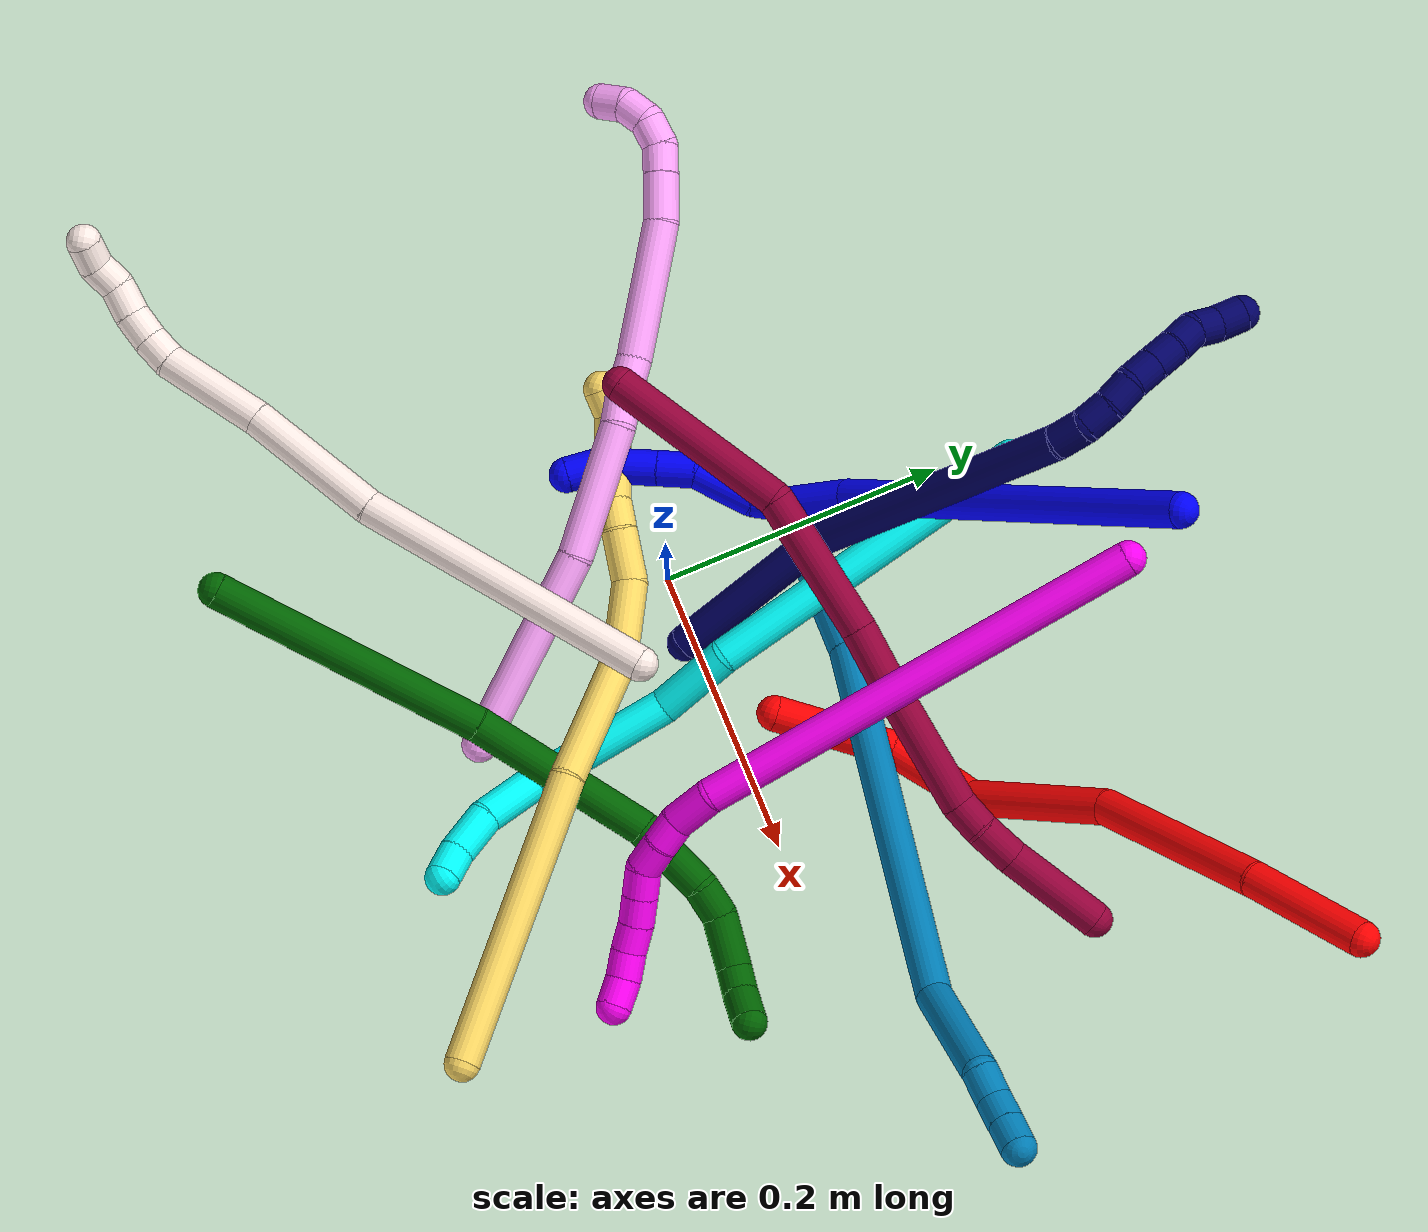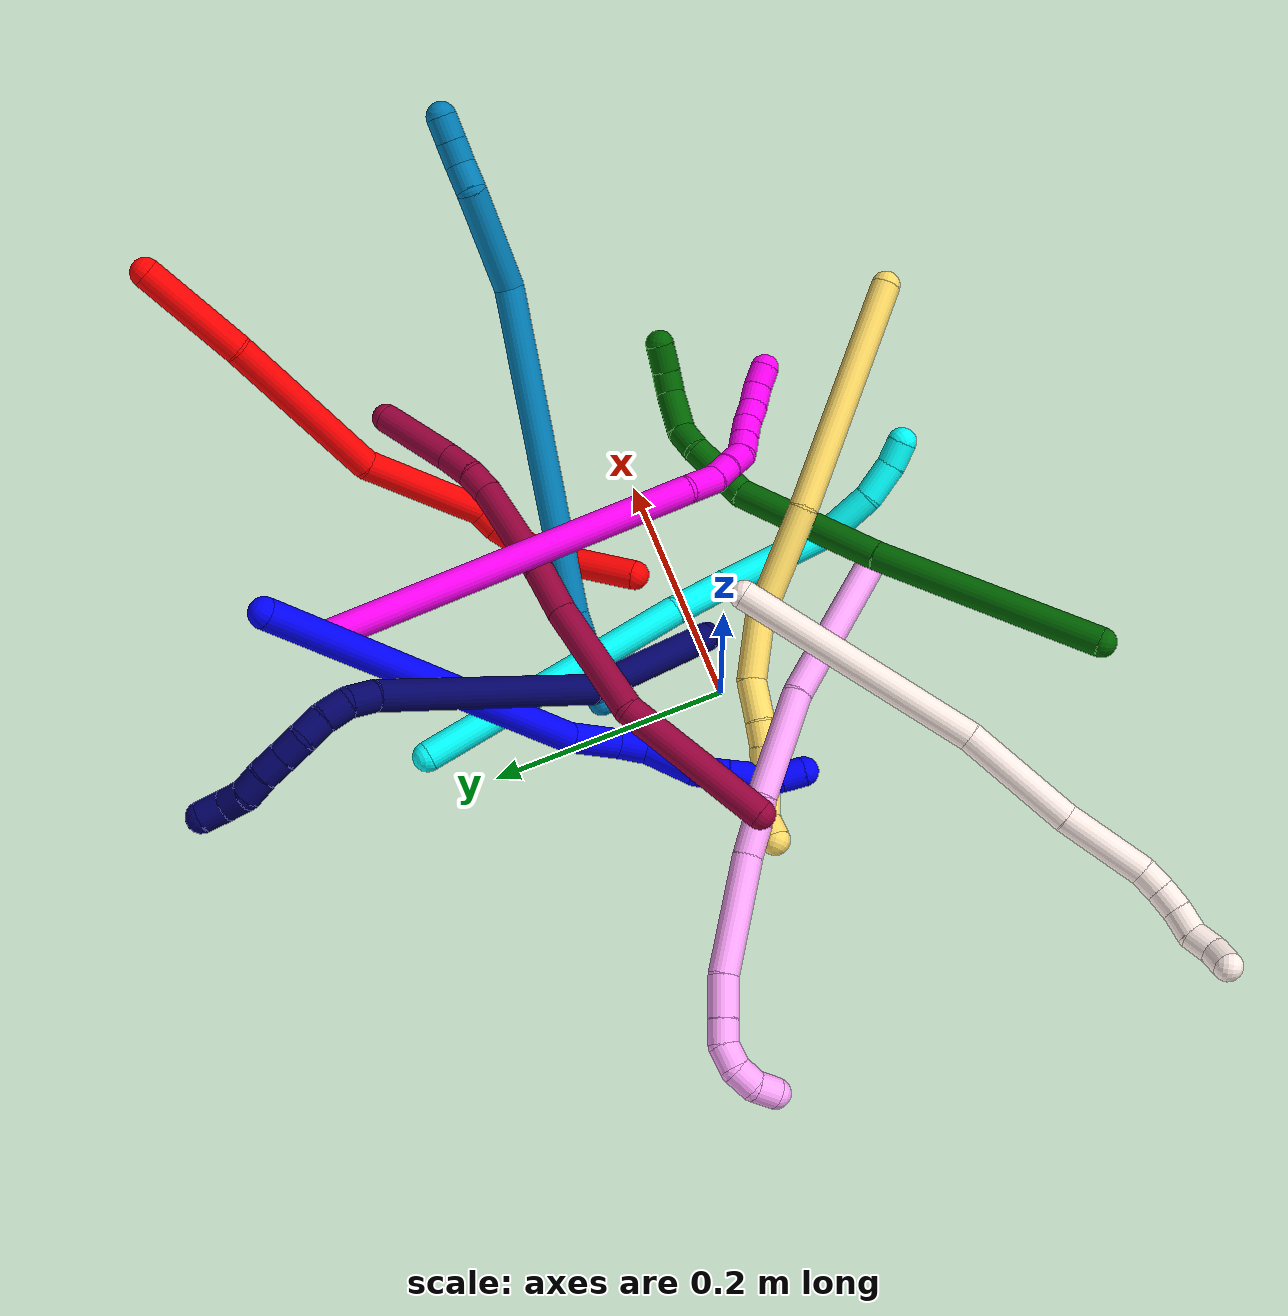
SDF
<sdf version="1.7">
 <world name="default">
  <plugin name="TubeGeneratorPlugin" filename="libtube_generator_plugin.so"/>
  <model name="photoneo_s_sensor">
   <static>1</static>
   <pose>0 0 2 1.57079 1.57079 3.14159</pose>
   <link name="link">
    <inertial><mass>0.1</mass></inertial>
    <sensor name="sensor" type="depth">
     <update_rate>30</update_rate>
     <camera>
      <horizontal_fov>1.22</horizontal_fov>
      <image><width>1920</width><height>1200</height><format>B8G8R8</format></image>
      <clip><near>0.1</near><far>4</far></clip>
      <depth_camera><output>points</output></depth_camera>
     </camera>
     <plugin name="camera_plugin" filename="libgazebo_ros_depth_camera.so">
      <baseline>0.2</baseline>
      <alwaysOn>1</alwaysOn>
      <updateRate>0.0</updateRate>
      <cameraName>camera_ir</cameraName>
      <imageTopicName>/camera/color/image_raw</imageTopicName>
      <cameraInfoTopicName>/camera/color/camera_info</cameraInfoTopicName>
      <depthImageTopicName>/camera/depth/image_raw</depthImageTopicName>
      <depthImageCameraInfoTopicName>/camera/depth/camera_info</depthImageCameraInfoTopicName>
      <pointCloudTopicName>/camera/depth/points</pointCloudTopicName>
      <frameName>fr_optical</frameName>
      <pointCloudCutoff>0.1</pointCloudCutoff>
      <pointCloudCutoffMax>2.0</pointCloudCutoffMax>
      <distortionK1>0</distortionK1>
      <distortionK2>0</distortionK2>
      <distortionK3>0</distortionK3>
      <distortionT1>0</distortionT1>
      <distortionT2>0</distortionT2>
      <CxPrime>0</CxPrime>
      <Cx>0</Cx>
      <Cy>0</Cy>
      <focalLength>0</focalLength>
      <hackBaseline>0</hackBaseline>
     </plugin>
    </sensor>
   </link>
  </model>
  <gravity>0 0 -9.8</gravity>
  <magnetic_field>6e-06 2.3e-05 -4.2e-05</magnetic_field>
  <atmosphere type="adiabatic"/>
  <physics name="default_physics" default="0" type="ode">
   <max_step_size>0.003</max_step_size>
   <real_time_factor>1</real_time_factor>
   <real_time_update_rate>1000</real_time_update_rate>
   <max_contacts>10000</max_contacts>
   <ode>
    <solver>
     <type>quick</type>
     <iters>100</iters>
     <sor>1.3</sor>
     <use_dynamic_moi_rescaling>0</use_dynamic_moi_rescaling>
    </solver>
    <constraints>
     <contact_max_correcting_vel>0</contact_max_correcting_vel>
     <contact_surface_layer>0.001</contact_surface_layer>
     <cfm>0</cfm>
     <erp>0.2</erp>
    </constraints>
   </ode>
  </physics>
  <scene><ambient>0.4 0.4 0.4 1</ambient><background>0.7 0.7 0.7 1</background><shadows>0</shadows></scene>
  <audio><device>default</device></audio>
  <spherical_coordinates>
   <surface_model>EARTH_WGS84</surface_model>
   <latitude_deg>0</latitude_deg>
   <longitude_deg>0</longitude_deg>
   <elevation>0</elevation>
   <heading_deg>0</heading_deg>
  </spherical_coordinates>
  <model name="bin">
   <static>1</static>
   <link name="bottom">
    <collision name="collision-bottom">
     <pose>0 0 -0.01 0 -0 0</pose>
     <geometry><box><size>0.8 0.6 0.02</size></box></geometry>
     <surface>
      <friction><ode><mu>100</mu><mu2>100</mu2></ode></friction>
      <contact><collide_bitmask>65535</collide_bitmask></contact>
     </surface>
    </collision>
   </link>
   <link name="west_wall">
    <collision name="collision-west_wall">
     <pose>-0.41 0 0.1 0 -0 0</pose>
     <geometry><box><size>0.02 0.6 0.2</size></box></geometry>
     <surface>
      <friction><ode><mu>100</mu><mu2>100</mu2></ode></friction>
      <contact><collide_bitmask>65535</collide_bitmask></contact>
     </surface>
    </collision>
   </link>
   <link name="east_wall">
    <collision name="collision-east_wall">
     <pose>0.41 0 0.1 0 -0 0</pose>
     <geometry><box><size>0.02 0.6 0.2</size></box></geometry>
     <surface>
      <friction><ode><mu>100</mu><mu2>100</mu2></ode></friction>
      <contact><collide_bitmask>65535</collide_bitmask></contact>
     </surface>
    </collision>
   </link>
   <link name="south_wall">
    <collision name="collision-south_wall">
     <pose>0 -0.31 0.1 0 -0 0</pose>
     <geometry><box><size>0.8 0.02 0.2</size></box></geometry>
     <surface>
      <friction><ode><mu>100</mu><mu2>100</mu2></ode></friction>
      <contact><collide_bitmask>65535</collide_bitmask></contact>
     </surface>
    </collision>
   </link>
   <link name="north_wall">
    <collision name="collision-north_wall">
     <pose>0 0.31 0.1 0 -0 0</pose>
     <geometry><box><size>0.8 0.02 0.2</size></box></geometry>
     <surface>
      <friction><ode><mu>100</mu><mu2>100</mu2></ode></friction>
      <contact><collide_bitmask>65535</collide_bitmask></contact>
     </surface>
    </collision>
   </link>
  </model>
  <model name="1">
   <static>0</static>
   <link name="1">
    <collision name="collision-cylinder-e_1_1_4">
     <pose>0.015487 -0.008972 -0.145802 3.08013 0.105624 2.08817</pose>
     <geometry><cylinder><radius>0.0125</radius><length>0.293792</length></cylinder></geometry>
     <surface>
      <friction><ode><mu>1.16</mu><mu2>1.16</mu2><slip1>0</slip1><slip2>0</slip2></ode></friction>
      <contact><ode><kp>1e+06</kp><kd>1</kd><max_vel>0</max_vel><min_depth>0.001</min_depth></ode></contact>
     </surface>
    </collision>
    <visual name="visual-cylinder-e_1_1_4">
     <pose>0.015487 -0.008972 -0.145802 3.08013 0.105624 2.08817</pose>
     <geometry><cylinder><radius>0.0125</radius><length>0.293792</length></cylinder></geometry>
     <material><ambient>0 0 1 1</ambient></material>
    </visual>
    <collision name="collision-cylinder-e_2_4_5">
     <pose>0.035038 -0.024712 -0.313242 2.83845 0.177366 1.05435</pose>
     <geometry><cylinder><radius>0.0125</radius><length>0.046067</length></cylinder></geometry>
     <surface>
      <friction><ode><mu>1.16</mu><mu2>1.16</mu2><slip1>0</slip1><slip2>0</slip2></ode></friction>
      <contact><ode><kp>1e+06</kp><kd>1</kd><max_vel>0</max_vel><min_depth>0.001</min_depth></ode></contact>
     </surface>
    </collision>
    <visual name="visual-cylinder-e_2_4_5">
     <pose>0.035038 -0.024712 -0.313242 2.83845 0.177366 1.05435</pose>
     <geometry><cylinder><radius>0.0125</radius><length>0.046067</length></cylinder></geometry>
     <material><ambient>0 0 1 1</ambient></material>
    </visual>
    <collision name="collision-cylinder-e_3_5_6">
     <pose>0.036404 -0.038968 -0.345123 2.51037 -0.209485 -0.622949</pose>
     <geometry><cylinder><radius>0.0125</radius><length>0.025944</length></cylinder></geometry>
     <surface>
      <friction><ode><mu>1.16</mu><mu2>1.16</mu2><slip1>0</slip1><slip2>0</slip2></ode></friction>
      <contact><ode><kp>1e+06</kp><kd>1</kd><max_vel>0</max_vel><min_depth>0.001</min_depth></ode></contact>
     </surface>
    </collision>
    <visual name="visual-cylinder-e_3_5_6">
     <pose>0.036404 -0.038968 -0.345123 2.51037 -0.209485 -0.622949</pose>
     <geometry><cylinder><radius>0.0125</radius><length>0.025944</length></cylinder></geometry>
     <material><ambient>0 0 1 1</ambient></material>
    </visual>
    <collision name="collision-cylinder-e_4_6_7">
     <pose>0.021955 -0.057896 -0.37002 2.47874 -0.563728 -1.39907</pose>
     <geometry><cylinder><radius>0.0125</radius><length>0.043987</length></cylinder></geometry>
     <surface>
      <friction><ode><mu>1.16</mu><mu2>1.16</mu2><slip1>0</slip1><slip2>0</slip2></ode></friction>
      <contact><ode><kp>1e+06</kp><kd>1</kd><max_vel>0</max_vel><min_depth>0.001</min_depth></ode></contact>
     </surface>
    </collision>
    <visual name="visual-cylinder-e_4_6_7">
     <pose>0.021955 -0.057896 -0.37002 2.47874 -0.563728 -1.39907</pose>
     <geometry><cylinder><radius>0.0125</radius><length>0.043987</length></cylinder></geometry>
     <material><ambient>0 0 1 1</ambient></material>
    </visual>
    <collision name="collision-cylinder-e_5_7_8">
     <pose>0.008404 -0.077561 -0.394896 2.46401 -0.136244 -0.382511</pose>
     <geometry><cylinder><radius>0.0125</radius><length>0.026487</length></cylinder></geometry>
     <surface>
      <friction><ode><mu>1.16</mu><mu2>1.16</mu2><slip1>0</slip1><slip2>0</slip2></ode></friction>
      <contact><ode><kp>1e+06</kp><kd>1</kd><max_vel>0</max_vel><min_depth>0.001</min_depth></ode></contact>
     </surface>
    </collision>
    <visual name="visual-cylinder-e_5_7_8">
     <pose>0.008404 -0.077561 -0.394896 2.46401 -0.136244 -0.382511</pose>
     <geometry><cylinder><radius>0.0125</radius><length>0.026487</length></cylinder></geometry>
     <material><ambient>0 0 1 1</ambient></material>
    </visual>
    <collision name="collision-cylinder-e_6_8_9">
     <pose>0.00518 -0.092933 -0.414323 2.48143 -0.121655 -0.351838</pose>
     <geometry><cylinder><radius>0.0125</radius><length>0.02348</length></cylinder></geometry>
     <surface>
      <friction><ode><mu>1.16</mu><mu2>1.16</mu2><slip1>0</slip1><slip2>0</slip2></ode></friction>
      <contact><ode><kp>1e+06</kp><kd>1</kd><max_vel>0</max_vel><min_depth>0.001</min_depth></ode></contact>
     </surface>
    </collision>
    <visual name="visual-cylinder-e_6_8_9">
     <pose>0.00518 -0.092933 -0.414323 2.48143 -0.121655 -0.351838</pose>
     <geometry><cylinder><radius>0.0125</radius><length>0.02348</length></cylinder></geometry>
     <material><ambient>0 0 1 1</ambient></material>
    </visual>
    <collision name="collision-cylinder-e_7_9_10">
     <pose>0.002821 -0.106984 -0.430739 2.37796 -0.09333 -0.231571</pose>
     <geometry><cylinder><radius>0.0125</radius><length>0.020056</length></cylinder></geometry>
     <surface>
      <friction><ode><mu>1.16</mu><mu2>1.16</mu2><slip1>0</slip1><slip2>0</slip2></ode></friction>
      <contact><ode><kp>1e+06</kp><kd>1</kd><max_vel>0</max_vel><min_depth>0.001</min_depth></ode></contact>
     </surface>
    </collision>
    <visual name="visual-cylinder-e_7_9_10">
     <pose>0.002821 -0.106984 -0.430739 2.37796 -0.09333 -0.231571</pose>
     <geometry><cylinder><radius>0.0125</radius><length>0.020056</length></cylinder></geometry>
     <material><ambient>0 0 1 1</ambient></material>
    </visual>
    <collision name="collision-cylinder-e_8_10_2">
     <pose>0.003317 -0.121835 -0.444009 2.2221 0.14219 0.2857</pose>
     <geometry><cylinder><radius>0.0125</radius><length>0.020188</length></cylinder></geometry>
     <surface>
      <friction><ode><mu>1.16</mu><mu2>1.16</mu2><slip1>0</slip1><slip2>0</slip2></ode></friction>
      <contact><ode><kp>1e+06</kp><kd>1</kd><max_vel>0</max_vel><min_depth>0.001</min_depth></ode></contact>
     </surface>
    </collision>
    <visual name="visual-cylinder-e_8_10_2">
     <pose>0.003317 -0.121835 -0.444009 2.2221 0.14219 0.2857</pose>
     <geometry><cylinder><radius>0.0125</radius><length>0.020188</length></cylinder></geometry>
     <material><ambient>0 0 1 1</ambient></material>
    </visual>
    <collision name="collision-sphere-2">
     <pose>0.004748 -0.129782 -0.450066 0 -0 0</pose>
     <geometry><sphere><radius>0.0125</radius></sphere></geometry>
     <surface>
      <friction><ode><mu>1.16</mu><mu2>1.16</mu2><slip1>0</slip1><slip2>0</slip2></ode></friction>
      <contact><ode><kp>1e+06</kp><kd>1</kd><max_vel>0</max_vel><min_depth>0.001</min_depth></ode></contact>
     </surface>
    </collision>
    <visual name="visual-sphere-2">
     <pose>0.004748 -0.129782 -0.450066 0 -0 0</pose>
     <geometry><sphere><radius>0.0125</radius></sphere></geometry>
     <material><ambient>0 0 1 1</ambient></material>
    </visual>
    <collision name="collision-sphere-10">
     <pose>0.001887 -0.113888 -0.437951 0 -0 0</pose>
     <geometry><sphere><radius>0.0125</radius></sphere></geometry>
     <surface>
      <friction><ode><mu>1.16</mu><mu2>1.16</mu2><slip1>0</slip1><slip2>0</slip2></ode></friction>
      <contact><ode><kp>1e+06</kp><kd>1</kd><max_vel>0</max_vel><min_depth>0.001</min_depth></ode></contact>
     </surface>
    </collision>
    <visual name="visual-sphere-10">
     <pose>0.001887 -0.113888 -0.437951 0 -0 0</pose>
     <geometry><sphere><radius>0.0125</radius></sphere></geometry>
     <material><ambient>0 0 1 1</ambient></material>
    </visual>
    <collision name="collision-sphere-9">
     <pose>0.003756 -0.100079 -0.423528 0 -0 0</pose>
     <geometry><sphere><radius>0.0125</radius></sphere></geometry>
     <surface>
      <friction><ode><mu>1.16</mu><mu2>1.16</mu2><slip1>0</slip1><slip2>0</slip2></ode></friction>
      <contact><ode><kp>1e+06</kp><kd>1</kd><max_vel>0</max_vel><min_depth>0.001</min_depth></ode></contact>
     </surface>
    </collision>
    <visual name="visual-sphere-9">
     <pose>0.003756 -0.100079 -0.423528 0 -0 0</pose>
     <geometry><sphere><radius>0.0125</radius></sphere></geometry>
     <material><ambient>0 0 1 1</ambient></material>
    </visual>
    <collision name="collision-sphere-4">
     <pose>0.030974 -0.017944 -0.291603 0 -0 0</pose>
     <geometry><sphere><radius>0.0125</radius></sphere></geometry>
     <surface>
      <friction><ode><mu>1.16</mu><mu2>1.16</mu2><slip1>0</slip1><slip2>0</slip2></ode></friction>
      <contact><ode><kp>1e+06</kp><kd>1</kd><max_vel>0</max_vel><min_depth>0.001</min_depth></ode></contact>
     </surface>
    </collision>
    <visual name="visual-sphere-4">
     <pose>0.030974 -0.017944 -0.291603 0 -0 0</pose>
     <geometry><sphere><radius>0.0125</radius></sphere></geometry>
     <material><ambient>0 0 1 1</ambient></material>
    </visual>
    <collision name="collision-sphere-1">
     <geometry><sphere><radius>0.0125</radius></sphere></geometry>
     <surface>
      <friction><ode><mu>1.16</mu><mu2>1.16</mu2><slip1>0</slip1><slip2>0</slip2></ode></friction>
      <contact><ode><kp>1e+06</kp><kd>1</kd><max_vel>0</max_vel><min_depth>0.001</min_depth></ode></contact>
     </surface>
    </collision>
    <visual name="visual-sphere-1">
     <geometry><sphere><radius>0.0125</radius></sphere></geometry>
     <material><ambient>0 0 1 1</ambient></material>
    </visual>
    <collision name="collision-sphere-8">
     <pose>0.006605 -0.085787 -0.405118 0 -0 0</pose>
     <geometry><sphere><radius>0.0125</radius></sphere></geometry>
     <surface>
      <friction><ode><mu>1.16</mu><mu2>1.16</mu2><slip1>0</slip1><slip2>0</slip2></ode></friction>
      <contact><ode><kp>1e+06</kp><kd>1</kd><max_vel>0</max_vel><min_depth>0.001</min_depth></ode></contact>
     </surface>
    </collision>
    <visual name="visual-sphere-8">
     <pose>0.006605 -0.085787 -0.405118 0 -0 0</pose>
     <geometry><sphere><radius>0.0125</radius></sphere></geometry>
     <material><ambient>0 0 1 1</ambient></material>
    </visual>
    <collision name="collision-sphere-5">
     <pose>0.039102 -0.03148 -0.33488 0 -0 0</pose>
     <geometry><sphere><radius>0.0125</radius></sphere></geometry>
     <surface>
      <friction><ode><mu>1.16</mu><mu2>1.16</mu2><slip1>0</slip1><slip2>0</slip2></ode></friction>
      <contact><ode><kp>1e+06</kp><kd>1</kd><max_vel>0</max_vel><min_depth>0.001</min_depth></ode></contact>
     </surface>
    </collision>
    <visual name="visual-sphere-5">
     <pose>0.039102 -0.03148 -0.33488 0 -0 0</pose>
     <geometry><sphere><radius>0.0125</radius></sphere></geometry>
     <material><ambient>0 0 1 1</ambient></material>
    </visual>
    <collision name="collision-sphere-6">
     <pose>0.033707 -0.046456 -0.355366 0 -0 0</pose>
     <geometry><sphere><radius>0.0125</radius></sphere></geometry>
     <surface>
      <friction><ode><mu>1.16</mu><mu2>1.16</mu2><slip1>0</slip1><slip2>0</slip2></ode></friction>
      <contact><ode><kp>1e+06</kp><kd>1</kd><max_vel>0</max_vel><min_depth>0.001</min_depth></ode></contact>
     </surface>
    </collision>
    <visual name="visual-sphere-6">
     <pose>0.033707 -0.046456 -0.355366 0 -0 0</pose>
     <geometry><sphere><radius>0.0125</radius></sphere></geometry>
     <material><ambient>0 0 1 1</ambient></material>
    </visual>
    <collision name="collision-sphere-7">
     <pose>0.010203 -0.069336 -0.384674 0 -0 0</pose>
     <geometry><sphere><radius>0.0125</radius></sphere></geometry>
     <surface>
      <friction><ode><mu>1.16</mu><mu2>1.16</mu2><slip1>0</slip1><slip2>0</slip2></ode></friction>
      <contact><ode><kp>1e+06</kp><kd>1</kd><max_vel>0</max_vel><min_depth>0.001</min_depth></ode></contact>
     </surface>
    </collision>
    <visual name="visual-sphere-7">
     <pose>0.010203 -0.069336 -0.384674 0 -0 0</pose>
     <geometry><sphere><radius>0.0125</radius></sphere></geometry>
     <material><ambient>0 0 1 1</ambient></material>
    </visual>
    <inertial>
     <pose>0.017084 -0.032347 -0.240571 0 -0 0</pose>
     <mass>0.5</mass>
     <inertia>
      <ixx>0.000805</ixx>
      <ixy>0</ixy>
      <ixz>0</ixz>
      <iyy>0.002876</iyy>
      <iyz>0</iyz>
      <izz>-0.000111</izz>
     </inertia>
    </inertial>
   </link>
   <pose>0.113881 0.319058 0.23826 -0.735192 0.448173 -0.273323</pose>
  </model>
  <model name="2">
   <static>0</static>
   <link name="2">
    <collision name="collision-cylinder-e_1_1_4">
     <pose>-0.004031 0.005012 -0.045194 -3.03115 -0.088416 1.34978</pose>
     <geometry><cylinder><radius>0.0125</radius><length>0.091299</length></cylinder></geometry>
     <surface>
      <friction><ode><mu>1.16</mu><mu2>1.16</mu2><slip1>0</slip1><slip2>0</slip2></ode></friction>
      <contact><ode><kp>1e+06</kp><kd>1</kd><max_vel>0</max_vel><min_depth>0.001</min_depth></ode></contact>
     </surface>
    </collision>
    <visual name="visual-cylinder-e_1_1_4">
     <pose>-0.004031 0.005012 -0.045194 -3.03115 -0.088416 1.34978</pose>
     <geometry><cylinder><radius>0.0125</radius><length>0.091299</length></cylinder></geometry>
     <material><ambient>1 0 0 1</ambient></material>
    </visual>
    <collision name="collision-cylinder-e_2_4_5">
     <pose>-0.001862 0.026163 -0.160673 -2.91588 0.085767 -0.723866</pose>
     <geometry><cylinder><radius>0.0125</radius><length>0.144759</length></cylinder></geometry>
     <surface>
      <friction><ode><mu>1.16</mu><mu2>1.16</mu2><slip1>0</slip1><slip2>0</slip2></ode></friction>
      <contact><ode><kp>1e+06</kp><kd>1</kd><max_vel>0</max_vel><min_depth>0.001</min_depth></ode></contact>
     </surface>
    </collision>
    <visual name="visual-cylinder-e_2_4_5">
     <pose>-0.001862 0.026163 -0.160673 -2.91588 0.085767 -0.723866</pose>
     <geometry><cylinder><radius>0.0125</radius><length>0.144759</length></cylinder></geometry>
     <material><ambient>1 0 0 1</ambient></material>
    </visual>
    <collision name="collision-cylinder-e_3_5_6">
     <pose>0.017931 0.038652 -0.285043 3.07422 0.245681 2.6087</pose>
     <geometry><cylinder><radius>0.0125</radius><length>0.111774</length></cylinder></geometry>
     <surface>
      <friction><ode><mu>1.16</mu><mu2>1.16</mu2><slip1>0</slip1><slip2>0</slip2></ode></friction>
      <contact><ode><kp>1e+06</kp><kd>1</kd><max_vel>0</max_vel><min_depth>0.001</min_depth></ode></contact>
     </surface>
    </collision>
    <visual name="visual-cylinder-e_3_5_6">
     <pose>0.017931 0.038652 -0.285043 3.07422 0.245681 2.6087</pose>
     <geometry><cylinder><radius>0.0125</radius><length>0.111774</length></cylinder></geometry>
     <material><ambient>1 0 0 1</ambient></material>
    </visual>
    <collision name="collision-cylinder-e_4_6_7">
     <pose>0.030054 0.036857 -0.349381 -2.96261 -0.140176 1.3278</pose>
     <geometry><cylinder><radius>0.0125</radius><length>0.021042</length></cylinder></geometry>
     <surface>
      <friction><ode><mu>1.16</mu><mu2>1.16</mu2><slip1>0</slip1><slip2>0</slip2></ode></friction>
      <contact><ode><kp>1e+06</kp><kd>1</kd><max_vel>0</max_vel><min_depth>0.001</min_depth></ode></contact>
     </surface>
    </collision>
    <visual name="visual-cylinder-e_4_6_7">
     <pose>0.030054 0.036857 -0.349381 -2.96261 -0.140176 1.3278</pose>
     <geometry><cylinder><radius>0.0125</radius><length>0.021042</length></cylinder></geometry>
     <material><ambient>1 0 0 1</ambient></material>
    </visual>
    <collision name="collision-cylinder-e_5_7_8">
     <pose>0.018687 0.03421 -0.379901 2.92303 -0.444797 -2.23815</pose>
     <geometry><cylinder><radius>0.0125</radius><length>0.046002</length></cylinder></geometry>
     <surface>
      <friction><ode><mu>1.16</mu><mu2>1.16</mu2><slip1>0</slip1><slip2>0</slip2></ode></friction>
      <contact><ode><kp>1e+06</kp><kd>1</kd><max_vel>0</max_vel><min_depth>0.001</min_depth></ode></contact>
     </surface>
    </collision>
    <visual name="visual-cylinder-e_5_7_8">
     <pose>0.018687 0.03421 -0.379901 2.92303 -0.444797 -2.23815</pose>
     <geometry><cylinder><radius>0.0125</radius><length>0.046002</length></cylinder></geometry>
     <material><ambient>1 0 0 1</ambient></material>
    </visual>
    <collision name="collision-cylinder-e_6_8_2">
     <pose>-0.007356 0.007456 -0.43266 2.54108 -0.389107 -1.13353</pose>
     <geometry><cylinder><radius>0.0125</radius><length>0.085123</length></cylinder></geometry>
     <surface>
      <friction><ode><mu>1.16</mu><mu2>1.16</mu2><slip1>0</slip1><slip2>0</slip2></ode></friction>
      <contact><ode><kp>1e+06</kp><kd>1</kd><max_vel>0</max_vel><min_depth>0.001</min_depth></ode></contact>
     </surface>
    </collision>
    <visual name="visual-cylinder-e_6_8_2">
     <pose>-0.007356 0.007456 -0.43266 2.54108 -0.389107 -1.13353</pose>
     <geometry><cylinder><radius>0.0125</radius><length>0.085123</length></cylinder></geometry>
     <material><ambient>1 0 0 1</ambient></material>
    </visual>
    <collision name="collision-sphere-2">
     <pose>-0.023502 -0.014797 -0.465151 0 -0 0</pose>
     <geometry><sphere><radius>0.0125</radius></sphere></geometry>
     <surface>
      <friction><ode><mu>1.16</mu><mu2>1.16</mu2><slip1>0</slip1><slip2>0</slip2></ode></friction>
      <contact><ode><kp>1e+06</kp><kd>1</kd><max_vel>0</max_vel><min_depth>0.001</min_depth></ode></contact>
     </surface>
    </collision>
    <visual name="visual-sphere-2">
     <pose>-0.023502 -0.014797 -0.465151 0 -0 0</pose>
     <geometry><sphere><radius>0.0125</radius></sphere></geometry>
     <material><ambient>1 0 0 1</ambient></material>
    </visual>
    <collision name="collision-sphere-4">
     <pose>-0.008062 0.010024 -0.090389 0 -0 0</pose>
     <geometry><sphere><radius>0.0125</radius></sphere></geometry>
     <surface>
      <friction><ode><mu>1.16</mu><mu2>1.16</mu2><slip1>0</slip1><slip2>0</slip2></ode></friction>
      <contact><ode><kp>1e+06</kp><kd>1</kd><max_vel>0</max_vel><min_depth>0.001</min_depth></ode></contact>
     </surface>
    </collision>
    <visual name="visual-sphere-4">
     <pose>-0.008062 0.010024 -0.090389 0 -0 0</pose>
     <geometry><sphere><radius>0.0125</radius></sphere></geometry>
     <material><ambient>1 0 0 1</ambient></material>
    </visual>
    <collision name="collision-sphere-1">
     <geometry><sphere><radius>0.0125</radius></sphere></geometry>
     <surface>
      <friction><ode><mu>1.16</mu><mu2>1.16</mu2><slip1>0</slip1><slip2>0</slip2></ode></friction>
      <contact><ode><kp>1e+06</kp><kd>1</kd><max_vel>0</max_vel><min_depth>0.001</min_depth></ode></contact>
     </surface>
    </collision>
    <visual name="visual-sphere-1">
     <geometry><sphere><radius>0.0125</radius></sphere></geometry>
     <material><ambient>1 0 0 1</ambient></material>
    </visual>
    <collision name="collision-sphere-8">
     <pose>0.008791 0.029708 -0.40017 0 -0 0</pose>
     <geometry><sphere><radius>0.0125</radius></sphere></geometry>
     <surface>
      <friction><ode><mu>1.16</mu><mu2>1.16</mu2><slip1>0</slip1><slip2>0</slip2></ode></friction>
      <contact><ode><kp>1e+06</kp><kd>1</kd><max_vel>0</max_vel><min_depth>0.001</min_depth></ode></contact>
     </surface>
    </collision>
    <visual name="visual-sphere-8">
     <pose>0.008791 0.029708 -0.40017 0 -0 0</pose>
     <geometry><sphere><radius>0.0125</radius></sphere></geometry>
     <material><ambient>1 0 0 1</ambient></material>
    </visual>
    <collision name="collision-sphere-5">
     <pose>0.004339 0.042301 -0.230957 0 -0 0</pose>
     <geometry><sphere><radius>0.0125</radius></sphere></geometry>
     <surface>
      <friction><ode><mu>1.16</mu><mu2>1.16</mu2><slip1>0</slip1><slip2>0</slip2></ode></friction>
      <contact><ode><kp>1e+06</kp><kd>1</kd><max_vel>0</max_vel><min_depth>0.001</min_depth></ode></contact>
     </surface>
    </collision>
    <visual name="visual-sphere-5">
     <pose>0.004339 0.042301 -0.230957 0 -0 0</pose>
     <geometry><sphere><radius>0.0125</radius></sphere></geometry>
     <material><ambient>1 0 0 1</ambient></material>
    </visual>
    <collision name="collision-sphere-6">
     <pose>0.031524 0.035003 -0.339129 0 -0 0</pose>
     <geometry><sphere><radius>0.0125</radius></sphere></geometry>
     <surface>
      <friction><ode><mu>1.16</mu><mu2>1.16</mu2><slip1>0</slip1><slip2>0</slip2></ode></friction>
      <contact><ode><kp>1e+06</kp><kd>1</kd><max_vel>0</max_vel><min_depth>0.001</min_depth></ode></contact>
     </surface>
    </collision>
    <visual name="visual-sphere-6">
     <pose>0.031524 0.035003 -0.339129 0 -0 0</pose>
     <geometry><sphere><radius>0.0125</radius></sphere></geometry>
     <material><ambient>1 0 0 1</ambient></material>
    </visual>
    <collision name="collision-sphere-7">
     <pose>0.028584 0.038712 -0.359632 0 -0 0</pose>
     <geometry><sphere><radius>0.0125</radius></sphere></geometry>
     <surface>
      <friction><ode><mu>1.16</mu><mu2>1.16</mu2><slip1>0</slip1><slip2>0</slip2></ode></friction>
      <contact><ode><kp>1e+06</kp><kd>1</kd><max_vel>0</max_vel><min_depth>0.001</min_depth></ode></contact>
     </surface>
    </collision>
    <visual name="visual-sphere-7">
     <pose>0.028584 0.038712 -0.359632 0 -0 0</pose>
     <geometry><sphere><radius>0.0125</radius></sphere></geometry>
     <material><ambient>1 0 0 1</ambient></material>
    </visual>
    <inertial>
     <pose>0.004465 0.023098 -0.241806 0 -0 0</pose>
     <mass>0.5</mass>
     <inertia>
      <ixx>2.4e-05</ixx>
      <ixy>0</ixy>
      <ixz>0</ixz>
      <iyy>-0.000195</iyy>
      <iyz>0</iyz>
      <izz>-8.4e-05</izz>
     </inertia>
    </inertial>
   </link>
   <pose>0.418424 0.317921 0.234718 -0.861627 0.694262 -0.298348</pose>
  </model>
  <model name="3">
   <static>0</static>
   <link name="3">
    <collision name="collision-cylinder-e_1_1_4">
     <pose>-0.001042 -0.035317 -0.113741 2.84052 -0.008745 -0.057636</pose>
     <geometry><cylinder><radius>0.0125</radius><length>0.238205</length></cylinder></geometry>
     <surface>
      <friction><ode><mu>1.16</mu><mu2>1.16</mu2><slip1>0</slip1><slip2>0</slip2></ode></friction>
      <contact><ode><kp>1e+06</kp><kd>1</kd><max_vel>0</max_vel><min_depth>0.001</min_depth></ode></contact>
     </surface>
    </collision>
    <visual name="visual-cylinder-e_1_1_4">
     <pose>-0.001042 -0.035317 -0.113741 2.84052 -0.008745 -0.057636</pose>
     <geometry><cylinder><radius>0.0125</radius><length>0.238205</length></cylinder></geometry>
     <material><ambient>0.003922 1 0.996078 1</ambient></material>
    </visual>
    <collision name="collision-cylinder-e_2_4_5">
     <pose>0.001298 -0.070559 -0.25541 -3.13887 0.120471 -3.09639</pose>
     <geometry><cylinder><radius>0.0125</radius><length>0.056265</length></cylinder></geometry>
     <surface>
      <friction><ode><mu>1.16</mu><mu2>1.16</mu2><slip1>0</slip1><slip2>0</slip2></ode></friction>
      <contact><ode><kp>1e+06</kp><kd>1</kd><max_vel>0</max_vel><min_depth>0.001</min_depth></ode></contact>
     </surface>
    </collision>
    <visual name="visual-cylinder-e_2_4_5">
     <pose>0.001298 -0.070559 -0.25541 -3.13887 0.120471 -3.09639</pose>
     <geometry><cylinder><radius>0.0125</radius><length>0.056265</length></cylinder></geometry>
     <material><ambient>0.003922 1 0.996078 1</ambient></material>
    </visual>
    <collision name="collision-cylinder-e_3_5_6">
     <pose>0.000401 -0.085162 -0.332897 2.85361 -0.082584 -0.555178</pose>
     <geometry><cylinder><radius>0.0125</radius><length>0.103727</length></cylinder></geometry>
     <surface>
      <friction><ode><mu>1.16</mu><mu2>1.16</mu2><slip1>0</slip1><slip2>0</slip2></ode></friction>
      <contact><ode><kp>1e+06</kp><kd>1</kd><max_vel>0</max_vel><min_depth>0.001</min_depth></ode></contact>
     </surface>
    </collision>
    <visual name="visual-cylinder-e_3_5_6">
     <pose>0.000401 -0.085162 -0.332897 2.85361 -0.082584 -0.555178</pose>
     <geometry><cylinder><radius>0.0125</radius><length>0.103727</length></cylinder></geometry>
     <material><ambient>0.003922 1 0.996078 1</ambient></material>
    </visual>
    <collision name="collision-cylinder-e_4_6_7">
     <pose>-0.005643 -0.116365 -0.398438 2.33957 -0.076636 -0.180348</pose>
     <geometry><cylinder><radius>0.0125</radius><length>0.04611</length></cylinder></geometry>
     <surface>
      <friction><ode><mu>1.16</mu><mu2>1.16</mu2><slip1>0</slip1><slip2>0</slip2></ode></friction>
      <contact><ode><kp>1e+06</kp><kd>1</kd><max_vel>0</max_vel><min_depth>0.001</min_depth></ode></contact>
     </surface>
    </collision>
    <visual name="visual-cylinder-e_4_6_7">
     <pose>-0.005643 -0.116365 -0.398438 2.33957 -0.076636 -0.180348</pose>
     <geometry><cylinder><radius>0.0125</radius><length>0.04611</length></cylinder></geometry>
     <material><ambient>0.003922 1 0.996078 1</ambient></material>
    </visual>
    <collision name="collision-cylinder-e_5_7_8">
     <pose>-0.004231 -0.144817 -0.425816 2.33333 0.190245 0.438994</pose>
     <geometry><cylinder><radius>0.0125</radius><length>0.033602</length></cylinder></geometry>
     <surface>
      <friction><ode><mu>1.16</mu><mu2>1.16</mu2><slip1>0</slip1><slip2>0</slip2></ode></friction>
      <contact><ode><kp>1e+06</kp><kd>1</kd><max_vel>0</max_vel><min_depth>0.001</min_depth></ode></contact>
     </surface>
    </collision>
    <visual name="visual-cylinder-e_5_7_8">
     <pose>-0.004231 -0.144817 -0.425816 2.33333 0.190245 0.438994</pose>
     <geometry><cylinder><radius>0.0125</radius><length>0.033602</length></cylinder></geometry>
     <material><ambient>0.003922 1 0.996078 1</ambient></material>
    </visual>
    <collision name="collision-cylinder-e_6_8_2">
     <pose>0.002168 -0.165605 -0.44297 2.14717 0.296 0.536224</pose>
     <geometry><cylinder><radius>0.0125</radius><length>0.02209</length></cylinder></geometry>
     <surface>
      <friction><ode><mu>1.16</mu><mu2>1.16</mu2><slip1>0</slip1><slip2>0</slip2></ode></friction>
      <contact><ode><kp>1e+06</kp><kd>1</kd><max_vel>0</max_vel><min_depth>0.001</min_depth></ode></contact>
     </surface>
    </collision>
    <visual name="visual-cylinder-e_6_8_2">
     <pose>0.002168 -0.165605 -0.44297 2.14717 0.296 0.536224</pose>
     <geometry><cylinder><radius>0.0125</radius><length>0.02209</length></cylinder></geometry>
     <material><ambient>0.003922 1 0.996078 1</ambient></material>
    </visual>
    <collision name="collision-sphere-2">
     <pose>0.00539 -0.174463 -0.448727 0 -0 0</pose>
     <geometry><sphere><radius>0.0125</radius></sphere></geometry>
     <surface>
      <friction><ode><mu>1.16</mu><mu2>1.16</mu2><slip1>0</slip1><slip2>0</slip2></ode></friction>
      <contact><ode><kp>1e+06</kp><kd>1</kd><max_vel>0</max_vel><min_depth>0.001</min_depth></ode></contact>
     </surface>
    </collision>
    <visual name="visual-sphere-2">
     <pose>0.00539 -0.174463 -0.448727 0 -0 0</pose>
     <geometry><sphere><radius>0.0125</radius></sphere></geometry>
     <material><ambient>0.003922 1 0.996078 1</ambient></material>
    </visual>
    <collision name="collision-sphere-4">
     <pose>-0.002083 -0.070635 -0.227482 0 -0 0</pose>
     <geometry><sphere><radius>0.0125</radius></sphere></geometry>
     <surface>
      <friction><ode><mu>1.16</mu><mu2>1.16</mu2><slip1>0</slip1><slip2>0</slip2></ode></friction>
      <contact><ode><kp>1e+06</kp><kd>1</kd><max_vel>0</max_vel><min_depth>0.001</min_depth></ode></contact>
     </surface>
    </collision>
    <visual name="visual-sphere-4">
     <pose>-0.002083 -0.070635 -0.227482 0 -0 0</pose>
     <geometry><sphere><radius>0.0125</radius></sphere></geometry>
     <material><ambient>0.003922 1 0.996078 1</ambient></material>
    </visual>
    <collision name="collision-sphere-1">
     <geometry><sphere><radius>0.0125</radius></sphere></geometry>
     <surface>
      <friction><ode><mu>1.16</mu><mu2>1.16</mu2><slip1>0</slip1><slip2>0</slip2></ode></friction>
      <contact><ode><kp>1e+06</kp><kd>1</kd><max_vel>0</max_vel><min_depth>0.001</min_depth></ode></contact>
     </surface>
    </collision>
    <visual name="visual-sphere-1">
     <geometry><sphere><radius>0.0125</radius></sphere></geometry>
     <material><ambient>0.003922 1 0.996078 1</ambient></material>
    </visual>
    <collision name="collision-sphere-8">
     <pose>-0.001054 -0.156747 -0.437212 0 -0 0</pose>
     <geometry><sphere><radius>0.0125</radius></sphere></geometry>
     <surface>
      <friction><ode><mu>1.16</mu><mu2>1.16</mu2><slip1>0</slip1><slip2>0</slip2></ode></friction>
      <contact><ode><kp>1e+06</kp><kd>1</kd><max_vel>0</max_vel><min_depth>0.001</min_depth></ode></contact>
     </surface>
    </collision>
    <visual name="visual-sphere-8">
     <pose>-0.001054 -0.156747 -0.437212 0 -0 0</pose>
     <geometry><sphere><radius>0.0125</radius></sphere></geometry>
     <material><ambient>0.003922 1 0.996078 1</ambient></material>
    </visual>
    <collision name="collision-sphere-5">
     <pose>0.004679 -0.070483 -0.283339 0 -0 0</pose>
     <geometry><sphere><radius>0.0125</radius></sphere></geometry>
     <surface>
      <friction><ode><mu>1.16</mu><mu2>1.16</mu2><slip1>0</slip1><slip2>0</slip2></ode></friction>
      <contact><ode><kp>1e+06</kp><kd>1</kd><max_vel>0</max_vel><min_depth>0.001</min_depth></ode></contact>
     </surface>
    </collision>
    <visual name="visual-sphere-5">
     <pose>0.004679 -0.070483 -0.283339 0 -0 0</pose>
     <geometry><sphere><radius>0.0125</radius></sphere></geometry>
     <material><ambient>0.003922 1 0.996078 1</ambient></material>
    </visual>
    <collision name="collision-sphere-6">
     <pose>-0.003878 -0.099842 -0.382456 0 -0 0</pose>
     <geometry><sphere><radius>0.0125</radius></sphere></geometry>
     <surface>
      <friction><ode><mu>1.16</mu><mu2>1.16</mu2><slip1>0</slip1><slip2>0</slip2></ode></friction>
      <contact><ode><kp>1e+06</kp><kd>1</kd><max_vel>0</max_vel><min_depth>0.001</min_depth></ode></contact>
     </surface>
    </collision>
    <visual name="visual-sphere-6">
     <pose>-0.003878 -0.099842 -0.382456 0 -0 0</pose>
     <geometry><sphere><radius>0.0125</radius></sphere></geometry>
     <material><ambient>0.003922 1 0.996078 1</ambient></material>
    </visual>
    <collision name="collision-sphere-7">
     <pose>-0.007408 -0.132888 -0.41442 0 -0 0</pose>
     <geometry><sphere><radius>0.0125</radius></sphere></geometry>
     <surface>
      <friction><ode><mu>1.16</mu><mu2>1.16</mu2><slip1>0</slip1><slip2>0</slip2></ode></friction>
      <contact><ode><kp>1e+06</kp><kd>1</kd><max_vel>0</max_vel><min_depth>0.001</min_depth></ode></contact>
     </surface>
    </collision>
    <visual name="visual-sphere-7">
     <pose>-0.007408 -0.132888 -0.41442 0 -0 0</pose>
     <geometry><sphere><radius>0.0125</radius></sphere></geometry>
     <material><ambient>0.003922 1 0.996078 1</ambient></material>
    </visual>
    <inertial>
     <pose>-0.000976 -0.070213 -0.236921 0 -0 0</pose>
     <mass>0.5</mass>
     <inertia>
      <ixx>0.001098</ixx>
      <ixy>0</ixy>
      <ixz>0</ixz>
      <iyy>-0.001283</iyy>
      <iyz>0</iyz>
      <izz>0.000356</izz>
     </inertia>
    </inertial>
   </link>
   <pose>0.019487 0.246126 0.063926 -1.17681 0.23354 0.236943</pose>
  </model>
  <model name="4">
   <static>0</static>
   <link name="4">
    <collision name="collision-cylinder-e_1_1_4">
     <pose>-0.043474 0.055784 -0.015827 -1.84726 -0.643337 0.830596</pose>
     <geometry><cylinder><radius>0.0125</radius><length>0.144947</length></cylinder></geometry>
     <surface>
      <friction><ode><mu>1.16</mu><mu2>1.16</mu2><slip1>0</slip1><slip2>0</slip2></ode></friction>
      <contact><ode><kp>1e+06</kp><kd>1</kd><max_vel>0</max_vel><min_depth>0.001</min_depth></ode></contact>
     </surface>
    </collision>
    <visual name="visual-cylinder-e_1_1_4">
     <pose>-0.043474 0.055784 -0.015827 -1.84726 -0.643337 0.830596</pose>
     <geometry><cylinder><radius>0.0125</radius><length>0.144947</length></cylinder></geometry>
     <material><ambient>1 0.65098 0.996078 1</ambient></material>
    </visual>
    <collision name="collision-cylinder-e_2_4_5">
     <pose>-0.119886 0.14527 -0.034392 -1.65183 -0.77228 0.830532</pose>
     <geometry><cylinder><radius>0.0125</radius><length>0.094407</length></cylinder></geometry>
     <surface>
      <friction><ode><mu>1.16</mu><mu2>1.16</mu2><slip1>0</slip1><slip2>0</slip2></ode></friction>
      <contact><ode><kp>1e+06</kp><kd>1</kd><max_vel>0</max_vel><min_depth>0.001</min_depth></ode></contact>
     </surface>
    </collision>
    <visual name="visual-cylinder-e_2_4_5">
     <pose>-0.119886 0.14527 -0.034392 -1.65183 -0.77228 0.830532</pose>
     <geometry><cylinder><radius>0.0125</radius><length>0.094407</length></cylinder></geometry>
     <material><ambient>1 0.65098 0.996078 1</ambient></material>
    </visual>
    <collision name="collision-cylinder-e_3_5_6">
     <pose>-0.161853 0.184849 -0.036068 -1.39227 -0.986487 0.844444</pose>
     <geometry><cylinder><radius>0.0125</radius><length>0.021653</length></cylinder></geometry>
     <surface>
      <friction><ode><mu>1.16</mu><mu2>1.16</mu2><slip1>0</slip1><slip2>0</slip2></ode></friction>
      <contact><ode><kp>1e+06</kp><kd>1</kd><max_vel>0</max_vel><min_depth>0.001</min_depth></ode></contact>
     </surface>
    </collision>
    <visual name="visual-cylinder-e_3_5_6">
     <pose>-0.161853 0.184849 -0.036068 -1.39227 -0.986487 0.844444</pose>
     <geometry><cylinder><radius>0.0125</radius><length>0.021653</length></cylinder></geometry>
     <material><ambient>1 0.65098 0.996078 1</ambient></material>
    </visual>
    <collision name="collision-cylinder-e_4_6_7">
     <pose>-0.181928 0.198575 -0.035266 -1.60374 -0.952697 0.979807</pose>
     <geometry><cylinder><radius>0.0125</radius><length>0.027103</length></cylinder></geometry>
     <surface>
      <friction><ode><mu>1.16</mu><mu2>1.16</mu2><slip1>0</slip1><slip2>0</slip2></ode></friction>
      <contact><ode><kp>1e+06</kp><kd>1</kd><max_vel>0</max_vel><min_depth>0.001</min_depth></ode></contact>
     </surface>
    </collision>
    <visual name="visual-cylinder-e_4_6_7">
     <pose>-0.181928 0.198575 -0.035266 -1.60374 -0.952697 0.979807</pose>
     <geometry><cylinder><radius>0.0125</radius><length>0.027103</length></cylinder></geometry>
     <material><ambient>1 0.65098 0.996078 1</ambient></material>
    </visual>
    <collision name="collision-cylinder-e_5_7_8">
     <pose>-0.22896 0.23917 -0.032321 -1.47326 -0.830148 0.760433</pose>
     <geometry><cylinder><radius>0.0125</radius><length>0.097526</length></cylinder></geometry>
     <surface>
      <friction><ode><mu>1.16</mu><mu2>1.16</mu2><slip1>0</slip1><slip2>0</slip2></ode></friction>
      <contact><ode><kp>1e+06</kp><kd>1</kd><max_vel>0</max_vel><min_depth>0.001</min_depth></ode></contact>
     </surface>
    </collision>
    <visual name="visual-cylinder-e_5_7_8">
     <pose>-0.22896 0.23917 -0.032321 -1.47326 -0.830148 0.760433</pose>
     <geometry><cylinder><radius>0.0125</radius><length>0.097526</length></cylinder></geometry>
     <material><ambient>1 0.65098 0.996078 1</ambient></material>
    </visual>
    <collision name="collision-cylinder-e_6_8_9">
     <pose>-0.277568 0.282285 -0.024687 -1.167 -0.84161 0.57457</pose>
     <geometry><cylinder><radius>0.0125</radius><length>0.033844</length></cylinder></geometry>
     <surface>
      <friction><ode><mu>1.16</mu><mu2>1.16</mu2><slip1>0</slip1><slip2>0</slip2></ode></friction>
      <contact><ode><kp>1e+06</kp><kd>1</kd><max_vel>0</max_vel><min_depth>0.001</min_depth></ode></contact>
     </surface>
    </collision>
    <visual name="visual-cylinder-e_6_8_9">
     <pose>-0.277568 0.282285 -0.024687 -1.167 -0.84161 0.57457</pose>
     <geometry><cylinder><radius>0.0125</radius><length>0.033844</length></cylinder></geometry>
     <material><ambient>1 0.65098 0.996078 1</ambient></material>
    </visual>
    <collision name="collision-cylinder-e_7_9_10">
     <pose>-0.297928 0.298648 -0.017486 -1.13787 -0.864425 0.573702</pose>
     <geometry><cylinder><radius>0.0125</radius><length>0.020352</length></cylinder></geometry>
     <surface>
      <friction><ode><mu>1.16</mu><mu2>1.16</mu2><slip1>0</slip1><slip2>0</slip2></ode></friction>
      <contact><ode><kp>1e+06</kp><kd>1</kd><max_vel>0</max_vel><min_depth>0.001</min_depth></ode></contact>
     </surface>
    </collision>
    <visual name="visual-cylinder-e_7_9_10">
     <pose>-0.297928 0.298648 -0.017486 -1.13787 -0.864425 0.573702</pose>
     <geometry><cylinder><radius>0.0125</radius><length>0.020352</length></cylinder></geometry>
     <material><ambient>1 0.65098 0.996078 1</ambient></material>
    </visual>
    <collision name="collision-cylinder-e_8_10_11">
     <pose>-0.31118 0.309744 -0.008024 -0.651213 -0.579948 0.200806</pose>
     <geometry><cylinder><radius>0.0125</radius><length>0.020115</length></cylinder></geometry>
     <surface>
      <friction><ode><mu>1.16</mu><mu2>1.16</mu2><slip1>0</slip1><slip2>0</slip2></ode></friction>
      <contact><ode><kp>1e+06</kp><kd>1</kd><max_vel>0</max_vel><min_depth>0.001</min_depth></ode></contact>
     </surface>
    </collision>
    <visual name="visual-cylinder-e_8_10_11">
     <pose>-0.31118 0.309744 -0.008024 -0.651213 -0.579948 0.200806</pose>
     <geometry><cylinder><radius>0.0125</radius><length>0.020115</length></cylinder></geometry>
     <material><ambient>1 0.65098 0.996078 1</ambient></material>
    </visual>
    <collision name="collision-cylinder-e_9_11_12">
     <pose>-0.32155 0.315364 0.007421 -0.059402 -0.505959 0.015361</pose>
     <geometry><cylinder><radius>0.0125</radius><length>0.020049</length></cylinder></geometry>
     <surface>
      <friction><ode><mu>1.16</mu><mu2>1.16</mu2><slip1>0</slip1><slip2>0</slip2></ode></friction>
      <contact><ode><kp>1e+06</kp><kd>1</kd><max_vel>0</max_vel><min_depth>0.001</min_depth></ode></contact>
     </surface>
    </collision>
    <visual name="visual-cylinder-e_9_11_12">
     <pose>-0.32155 0.315364 0.007421 -0.059402 -0.505959 0.015361</pose>
     <geometry><cylinder><radius>0.0125</radius><length>0.020049</length></cylinder></geometry>
     <material><ambient>1 0.65098 0.996078 1</ambient></material>
    </visual>
    <collision name="collision-cylinder-e_10_12_2">
     <pose>-0.329497 0.312341 0.025003 0.381588 -0.313934 -0.061118</pose>
     <geometry><cylinder><radius>0.0125</radius><length>0.020006</length></cylinder></geometry>
     <surface>
      <friction><ode><mu>1.16</mu><mu2>1.16</mu2><slip1>0</slip1><slip2>0</slip2></ode></friction>
      <contact><ode><kp>1e+06</kp><kd>1</kd><max_vel>0</max_vel><min_depth>0.001</min_depth></ode></contact>
     </surface>
    </collision>
    <visual name="visual-cylinder-e_10_12_2">
     <pose>-0.329497 0.312341 0.025003 0.381588 -0.313934 -0.061118</pose>
     <geometry><cylinder><radius>0.0125</radius><length>0.020006</length></cylinder></geometry>
     <material><ambient>1 0.65098 0.996078 1</ambient></material>
    </visual>
    <collision name="collision-sphere-2">
     <pose>-0.332586 0.308799 0.033833 0 -0 0</pose>
     <geometry><sphere><radius>0.0125</radius></sphere></geometry>
     <surface>
      <friction><ode><mu>1.16</mu><mu2>1.16</mu2><slip1>0</slip1><slip2>0</slip2></ode></friction>
      <contact><ode><kp>1e+06</kp><kd>1</kd><max_vel>0</max_vel><min_depth>0.001</min_depth></ode></contact>
     </surface>
    </collision>
    <visual name="visual-sphere-2">
     <pose>-0.332586 0.308799 0.033833 0 -0 0</pose>
     <geometry><sphere><radius>0.0125</radius></sphere></geometry>
     <material><ambient>1 0.65098 0.996078 1</ambient></material>
    </visual>
    <collision name="collision-sphere-12">
     <pose>-0.326408 0.315884 0.016174 0 -0 0</pose>
     <geometry><sphere><radius>0.0125</radius></sphere></geometry>
     <surface>
      <friction><ode><mu>1.16</mu><mu2>1.16</mu2><slip1>0</slip1><slip2>0</slip2></ode></friction>
      <contact><ode><kp>1e+06</kp><kd>1</kd><max_vel>0</max_vel><min_depth>0.001</min_depth></ode></contact>
     </surface>
    </collision>
    <visual name="visual-sphere-12">
     <pose>-0.326408 0.315884 0.016174 0 -0 0</pose>
     <geometry><sphere><radius>0.0125</radius></sphere></geometry>
     <material><ambient>1 0.65098 0.996078 1</ambient></material>
    </visual>
    <collision name="collision-sphere-11">
     <pose>-0.316692 0.314843 -0.001332 0 -0 0</pose>
     <geometry><sphere><radius>0.0125</radius></sphere></geometry>
     <surface>
      <friction><ode><mu>1.16</mu><mu2>1.16</mu2><slip1>0</slip1><slip2>0</slip2></ode></friction>
      <contact><ode><kp>1e+06</kp><kd>1</kd><max_vel>0</max_vel><min_depth>0.001</min_depth></ode></contact>
     </surface>
    </collision>
    <visual name="visual-sphere-11">
     <pose>-0.316692 0.314843 -0.001332 0 -0 0</pose>
     <geometry><sphere><radius>0.0125</radius></sphere></geometry>
     <material><ambient>1 0.65098 0.996078 1</ambient></material>
    </visual>
    <collision name="collision-sphere-10">
     <pose>-0.305669 0.304644 -0.014715 0 -0 0</pose>
     <geometry><sphere><radius>0.0125</radius></sphere></geometry>
     <surface>
      <friction><ode><mu>1.16</mu><mu2>1.16</mu2><slip1>0</slip1><slip2>0</slip2></ode></friction>
      <contact><ode><kp>1e+06</kp><kd>1</kd><max_vel>0</max_vel><min_depth>0.001</min_depth></ode></contact>
     </surface>
    </collision>
    <visual name="visual-sphere-10">
     <pose>-0.305669 0.304644 -0.014715 0 -0 0</pose>
     <geometry><sphere><radius>0.0125</radius></sphere></geometry>
     <material><ambient>1 0.65098 0.996078 1</ambient></material>
    </visual>
    <collision name="collision-sphere-9">
     <pose>-0.290187 0.292653 -0.020257 0 -0 0</pose>
     <geometry><sphere><radius>0.0125</radius></sphere></geometry>
     <surface>
      <friction><ode><mu>1.16</mu><mu2>1.16</mu2><slip1>0</slip1><slip2>0</slip2></ode></friction>
      <contact><ode><kp>1e+06</kp><kd>1</kd><max_vel>0</max_vel><min_depth>0.001</min_depth></ode></contact>
     </surface>
    </collision>
    <visual name="visual-sphere-9">
     <pose>-0.290187 0.292653 -0.020257 0 -0 0</pose>
     <geometry><sphere><radius>0.0125</radius></sphere></geometry>
     <material><ambient>1 0.65098 0.996078 1</ambient></material>
    </visual>
    <collision name="collision-sphere-4">
     <pose>-0.086949 0.111568 -0.031655 0 -0 0</pose>
     <geometry><sphere><radius>0.0125</radius></sphere></geometry>
     <surface>
      <friction><ode><mu>1.16</mu><mu2>1.16</mu2><slip1>0</slip1><slip2>0</slip2></ode></friction>
      <contact><ode><kp>1e+06</kp><kd>1</kd><max_vel>0</max_vel><min_depth>0.001</min_depth></ode></contact>
     </surface>
    </collision>
    <visual name="visual-sphere-4">
     <pose>-0.086949 0.111568 -0.031655 0 -0 0</pose>
     <geometry><sphere><radius>0.0125</radius></sphere></geometry>
     <material><ambient>1 0.65098 0.996078 1</ambient></material>
    </visual>
    <collision name="collision-sphere-1">
     <geometry><sphere><radius>0.0125</radius></sphere></geometry>
     <surface>
      <friction><ode><mu>1.16</mu><mu2>1.16</mu2><slip1>0</slip1><slip2>0</slip2></ode></friction>
      <contact><ode><kp>1e+06</kp><kd>1</kd><max_vel>0</max_vel><min_depth>0.001</min_depth></ode></contact>
     </surface>
    </collision>
    <visual name="visual-sphere-1">
     <geometry><sphere><radius>0.0125</radius></sphere></geometry>
     <material><ambient>1 0.65098 0.996078 1</ambient></material>
    </visual>
    <collision name="collision-sphere-8">
     <pose>-0.264949 0.271917 -0.029117 0 -0 0</pose>
     <geometry><sphere><radius>0.0125</radius></sphere></geometry>
     <surface>
      <friction><ode><mu>1.16</mu><mu2>1.16</mu2><slip1>0</slip1><slip2>0</slip2></ode></friction>
      <contact><ode><kp>1e+06</kp><kd>1</kd><max_vel>0</max_vel><min_depth>0.001</min_depth></ode></contact>
     </surface>
    </collision>
    <visual name="visual-sphere-8">
     <pose>-0.264949 0.271917 -0.029117 0 -0 0</pose>
     <geometry><sphere><radius>0.0125</radius></sphere></geometry>
     <material><ambient>1 0.65098 0.996078 1</ambient></material>
    </visual>
    <collision name="collision-sphere-5">
     <pose>-0.152823 0.178972 -0.037129 0 -0 0</pose>
     <geometry><sphere><radius>0.0125</radius></sphere></geometry>
     <surface>
      <friction><ode><mu>1.16</mu><mu2>1.16</mu2><slip1>0</slip1><slip2>0</slip2></ode></friction>
      <contact><ode><kp>1e+06</kp><kd>1</kd><max_vel>0</max_vel><min_depth>0.001</min_depth></ode></contact>
     </surface>
    </collision>
    <visual name="visual-sphere-5">
     <pose>-0.152823 0.178972 -0.037129 0 -0 0</pose>
     <geometry><sphere><radius>0.0125</radius></sphere></geometry>
     <material><ambient>1 0.65098 0.996078 1</ambient></material>
    </visual>
    <collision name="collision-sphere-6">
     <pose>-0.170884 0.190726 -0.035008 0 -0 0</pose>
     <geometry><sphere><radius>0.0125</radius></sphere></geometry>
     <surface>
      <friction><ode><mu>1.16</mu><mu2>1.16</mu2><slip1>0</slip1><slip2>0</slip2></ode></friction>
      <contact><ode><kp>1e+06</kp><kd>1</kd><max_vel>0</max_vel><min_depth>0.001</min_depth></ode></contact>
     </surface>
    </collision>
    <visual name="visual-sphere-6">
     <pose>-0.170884 0.190726 -0.035008 0 -0 0</pose>
     <geometry><sphere><radius>0.0125</radius></sphere></geometry>
     <material><ambient>1 0.65098 0.996078 1</ambient></material>
    </visual>
    <collision name="collision-sphere-7">
     <pose>-0.192972 0.206423 -0.035525 0 -0 0</pose>
     <geometry><sphere><radius>0.0125</radius></sphere></geometry>
     <surface>
      <friction><ode><mu>1.16</mu><mu2>1.16</mu2><slip1>0</slip1><slip2>0</slip2></ode></friction>
      <contact><ode><kp>1e+06</kp><kd>1</kd><max_vel>0</max_vel><min_depth>0.001</min_depth></ode></contact>
     </surface>
    </collision>
    <visual name="visual-sphere-7">
     <pose>-0.192972 0.206423 -0.035525 0 -0 0</pose>
     <geometry><sphere><radius>0.0125</radius></sphere></geometry>
     <material><ambient>1 0.65098 0.996078 1</ambient></material>
    </visual>
    <inertial>
     <pose>-0.166279 0.177887 -0.022267 0 -0 0</pose>
     <mass>0.5</mass>
     <inertia>
      <ixx>0.000432</ixx>
      <ixy>0</ixy>
      <ixz>0</ixz>
      <iyy>0.000413</iyy>
      <iyz>0</iyz>
      <izz>-3.4e-05</izz>
     </inertia>
    </inertial>
   </link>
   <pose>0.056853 -0.163211 0.01247 1.5816 -0.739604 -0.659775</pose>
  </model>
  <model name="5">
   <static>0</static>
   <link name="5">
    <collision name="collision-cylinder-e_1_1_4">
     <pose>0.005436 -0.005221 -0.104489 3.09167 0.051916 1.6099</pose>
     <geometry><cylinder><radius>0.0125</radius><length>0.209522</length></cylinder></geometry>
     <surface>
      <friction><ode><mu>1.16</mu><mu2>1.16</mu2><slip1>0</slip1><slip2>0</slip2></ode></friction>
      <contact><ode><kp>1e+06</kp><kd>1</kd><max_vel>0</max_vel><min_depth>0.001</min_depth></ode></contact>
     </surface>
    </collision>
    <visual name="visual-cylinder-e_1_1_4">
     <pose>0.005436 -0.005221 -0.104489 3.09167 0.051916 1.6099</pose>
     <geometry><cylinder><radius>0.0125</radius><length>0.209522</length></cylinder></geometry>
     <material><ambient>1 0.858824 0.4 1</ambient></material>
    </visual>
    <collision name="collision-cylinder-e_2_4_5">
     <pose>0.020184 -0.019241 -0.255222 2.95356 0.195295 1.60889</pose>
     <geometry><cylinder><radius>0.0125</radius><length>0.095971</length></cylinder></geometry>
     <surface>
      <friction><ode><mu>1.16</mu><mu2>1.16</mu2><slip1>0</slip1><slip2>0</slip2></ode></friction>
      <contact><ode><kp>1e+06</kp><kd>1</kd><max_vel>0</max_vel><min_depth>0.001</min_depth></ode></contact>
     </surface>
    </collision>
    <visual name="visual-cylinder-e_2_4_5">
     <pose>0.020184 -0.019241 -0.255222 2.95356 0.195295 1.60889</pose>
     <geometry><cylinder><radius>0.0125</radius><length>0.095971</length></cylinder></geometry>
     <material><ambient>1 0.858824 0.4 1</ambient></material>
    </visual>
    <collision name="collision-cylinder-e_3_5_6">
     <pose>0.026572 -0.033655 -0.328645 2.93791 -0.104964 -0.949583</pose>
     <geometry><cylinder><radius>0.0125</radius><length>0.055813</length></cylinder></geometry>
     <surface>
      <friction><ode><mu>1.16</mu><mu2>1.16</mu2><slip1>0</slip1><slip2>0</slip2></ode></friction>
      <contact><ode><kp>1e+06</kp><kd>1</kd><max_vel>0</max_vel><min_depth>0.001</min_depth></ode></contact>
     </surface>
    </collision>
    <visual name="visual-cylinder-e_3_5_6">
     <pose>0.026572 -0.033655 -0.328645 2.93791 -0.104964 -0.949583</pose>
     <geometry><cylinder><radius>0.0125</radius><length>0.055813</length></cylinder></geometry>
     <material><ambient>1 0.858824 0.4 1</ambient></material>
    </visual>
    <collision name="collision-cylinder-e_4_6_7">
     <pose>0.015272 -0.043309 -0.371732 2.89287 -0.471918 -2.18268</pose>
     <geometry><cylinder><radius>0.0125</radius><length>0.036855</length></cylinder></geometry>
     <surface>
      <friction><ode><mu>1.16</mu><mu2>1.16</mu2><slip1>0</slip1><slip2>0</slip2></ode></friction>
      <contact><ode><kp>1e+06</kp><kd>1</kd><max_vel>0</max_vel><min_depth>0.001</min_depth></ode></contact>
     </surface>
    </collision>
    <visual name="visual-cylinder-e_4_6_7">
     <pose>0.015272 -0.043309 -0.371732 2.89287 -0.471918 -2.18268</pose>
     <geometry><cylinder><radius>0.0125</radius><length>0.036855</length></cylinder></geometry>
     <material><ambient>1 0.858824 0.4 1</ambient></material>
    </visual>
    <collision name="collision-cylinder-e_5_7_8">
     <pose>0.003066 -0.050927 -0.396866 2.77168 -0.369186 -1.5688</pose>
     <geometry><cylinder><radius>0.0125</radius><length>0.02122</length></cylinder></geometry>
     <surface>
      <friction><ode><mu>1.16</mu><mu2>1.16</mu2><slip1>0</slip1><slip2>0</slip2></ode></friction>
      <contact><ode><kp>1e+06</kp><kd>1</kd><max_vel>0</max_vel><min_depth>0.001</min_depth></ode></contact>
     </surface>
    </collision>
    <visual name="visual-cylinder-e_5_7_8">
     <pose>0.003066 -0.050927 -0.396866 2.77168 -0.369186 -1.5688</pose>
     <geometry><cylinder><radius>0.0125</radius><length>0.02122</length></cylinder></geometry>
     <material><ambient>1 0.858824 0.4 1</ambient></material>
    </visual>
    <collision name="collision-cylinder-e_6_8_9">
     <pose>-0.003206 -0.057016 -0.415465 2.87977 -0.246662 -1.51056</pose>
     <geometry><cylinder><radius>0.0125</radius><length>0.020012</length></cylinder></geometry>
     <surface>
      <friction><ode><mu>1.16</mu><mu2>1.16</mu2><slip1>0</slip1><slip2>0</slip2></ode></friction>
      <contact><ode><kp>1e+06</kp><kd>1</kd><max_vel>0</max_vel><min_depth>0.001</min_depth></ode></contact>
     </surface>
    </collision>
    <visual name="visual-cylinder-e_6_8_9">
     <pose>-0.003206 -0.057016 -0.415465 2.87977 -0.246662 -1.51056</pose>
     <geometry><cylinder><radius>0.0125</radius><length>0.020012</length></cylinder></geometry>
     <material><ambient>1 0.858824 0.4 1</ambient></material>
    </visual>
    <collision name="collision-cylinder-e_7_9_10">
     <pose>-0.008954 -0.060522 -0.434458 3.03858 -0.32928 -2.53987</pose>
     <geometry><cylinder><radius>0.0125</radius><length>0.020441</length></cylinder></geometry>
     <surface>
      <friction><ode><mu>1.16</mu><mu2>1.16</mu2><slip1>0</slip1><slip2>0</slip2></ode></friction>
      <contact><ode><kp>1e+06</kp><kd>1</kd><max_vel>0</max_vel><min_depth>0.001</min_depth></ode></contact>
     </surface>
    </collision>
    <visual name="visual-cylinder-e_7_9_10">
     <pose>-0.008954 -0.060522 -0.434458 3.03858 -0.32928 -2.53987</pose>
     <geometry><cylinder><radius>0.0125</radius><length>0.020441</length></cylinder></geometry>
     <material><ambient>1 0.858824 0.4 1</ambient></material>
    </visual>
    <collision name="collision-cylinder-e_8_10_11">
     <pose>-0.015192 -0.063089 -0.453596 2.97787 -0.295145 -2.13294</pose>
     <geometry><cylinder><radius>0.0125</radius><length>0.020165</length></cylinder></geometry>
     <surface>
      <friction><ode><mu>1.16</mu><mu2>1.16</mu2><slip1>0</slip1><slip2>0</slip2></ode></friction>
      <contact><ode><kp>1e+06</kp><kd>1</kd><max_vel>0</max_vel><min_depth>0.001</min_depth></ode></contact>
     </surface>
    </collision>
    <visual name="visual-cylinder-e_8_10_11">
     <pose>-0.015192 -0.063089 -0.453596 2.97787 -0.295145 -2.13294</pose>
     <geometry><cylinder><radius>0.0125</radius><length>0.020165</length></cylinder></geometry>
     <material><ambient>1 0.858824 0.4 1</ambient></material>
    </visual>
    <collision name="collision-cylinder-e_9_11_2">
     <pose>-0.025153 -0.065701 -0.470151 2.9949 -0.779371 -2.78751</pose>
     <geometry><cylinder><radius>0.0125</radius><length>0.02</length></cylinder></geometry>
     <surface>
      <friction><ode><mu>1.16</mu><mu2>1.16</mu2><slip1>0</slip1><slip2>0</slip2></ode></friction>
      <contact><ode><kp>1e+06</kp><kd>1</kd><max_vel>0</max_vel><min_depth>0.001</min_depth></ode></contact>
     </surface>
    </collision>
    <visual name="visual-cylinder-e_9_11_2">
     <pose>-0.025153 -0.065701 -0.470151 2.9949 -0.779371 -2.78751</pose>
     <geometry><cylinder><radius>0.0125</radius><length>0.02</length></cylinder></geometry>
     <material><ambient>1 0.858824 0.4 1</ambient></material>
    </visual>
    <collision name="collision-sphere-2">
     <pose>-0.032182 -0.066741 -0.477188 0 -0 0</pose>
     <geometry><sphere><radius>0.0125</radius></sphere></geometry>
     <surface>
      <friction><ode><mu>1.16</mu><mu2>1.16</mu2><slip1>0</slip1><slip2>0</slip2></ode></friction>
      <contact><ode><kp>1e+06</kp><kd>1</kd><max_vel>0</max_vel><min_depth>0.001</min_depth></ode></contact>
     </surface>
    </collision>
    <visual name="visual-sphere-2">
     <pose>-0.032182 -0.066741 -0.477188 0 -0 0</pose>
     <geometry><sphere><radius>0.0125</radius></sphere></geometry>
     <material><ambient>1 0.858824 0.4 1</ambient></material>
    </visual>
    <collision name="collision-sphere-11">
     <pose>-0.018125 -0.064661 -0.463113 0 -0 0</pose>
     <geometry><sphere><radius>0.0125</radius></sphere></geometry>
     <surface>
      <friction><ode><mu>1.16</mu><mu2>1.16</mu2><slip1>0</slip1><slip2>0</slip2></ode></friction>
      <contact><ode><kp>1e+06</kp><kd>1</kd><max_vel>0</max_vel><min_depth>0.001</min_depth></ode></contact>
     </surface>
    </collision>
    <visual name="visual-sphere-11">
     <pose>-0.018125 -0.064661 -0.463113 0 -0 0</pose>
     <geometry><sphere><radius>0.0125</radius></sphere></geometry>
     <material><ambient>1 0.858824 0.4 1</ambient></material>
    </visual>
    <collision name="collision-sphere-10">
     <pose>-0.012259 -0.061517 -0.444078 0 -0 0</pose>
     <geometry><sphere><radius>0.0125</radius></sphere></geometry>
     <surface>
      <friction><ode><mu>1.16</mu><mu2>1.16</mu2><slip1>0</slip1><slip2>0</slip2></ode></friction>
      <contact><ode><kp>1e+06</kp><kd>1</kd><max_vel>0</max_vel><min_depth>0.001</min_depth></ode></contact>
     </surface>
    </collision>
    <visual name="visual-sphere-10">
     <pose>-0.012259 -0.061517 -0.444078 0 -0 0</pose>
     <geometry><sphere><radius>0.0125</radius></sphere></geometry>
     <material><ambient>1 0.858824 0.4 1</ambient></material>
    </visual>
    <collision name="collision-sphere-9">
     <pose>-0.005649 -0.059528 -0.424838 0 -0 0</pose>
     <geometry><sphere><radius>0.0125</radius></sphere></geometry>
     <surface>
      <friction><ode><mu>1.16</mu><mu2>1.16</mu2><slip1>0</slip1><slip2>0</slip2></ode></friction>
      <contact><ode><kp>1e+06</kp><kd>1</kd><max_vel>0</max_vel><min_depth>0.001</min_depth></ode></contact>
     </surface>
    </collision>
    <visual name="visual-sphere-9">
     <pose>-0.005649 -0.059528 -0.424838 0 -0 0</pose>
     <geometry><sphere><radius>0.0125</radius></sphere></geometry>
     <material><ambient>1 0.858824 0.4 1</ambient></material>
    </visual>
    <collision name="collision-sphere-4">
     <pose>0.010873 -0.010442 -0.208979 0 -0 0</pose>
     <geometry><sphere><radius>0.0125</radius></sphere></geometry>
     <surface>
      <friction><ode><mu>1.16</mu><mu2>1.16</mu2><slip1>0</slip1><slip2>0</slip2></ode></friction>
      <contact><ode><kp>1e+06</kp><kd>1</kd><max_vel>0</max_vel><min_depth>0.001</min_depth></ode></contact>
     </surface>
    </collision>
    <visual name="visual-sphere-4">
     <pose>0.010873 -0.010442 -0.208979 0 -0 0</pose>
     <geometry><sphere><radius>0.0125</radius></sphere></geometry>
     <material><ambient>1 0.858824 0.4 1</ambient></material>
    </visual>
    <collision name="collision-sphere-1">
     <geometry><sphere><radius>0.0125</radius></sphere></geometry>
     <surface>
      <friction><ode><mu>1.16</mu><mu2>1.16</mu2><slip1>0</slip1><slip2>0</slip2></ode></friction>
      <contact><ode><kp>1e+06</kp><kd>1</kd><max_vel>0</max_vel><min_depth>0.001</min_depth></ode></contact>
     </surface>
    </collision>
    <visual name="visual-sphere-1">
     <geometry><sphere><radius>0.0125</radius></sphere></geometry>
     <material><ambient>1 0.858824 0.4 1</ambient></material>
    </visual>
    <collision name="collision-sphere-8">
     <pose>-0.000763 -0.054505 -0.406092 0 -0 0</pose>
     <geometry><sphere><radius>0.0125</radius></sphere></geometry>
     <surface>
      <friction><ode><mu>1.16</mu><mu2>1.16</mu2><slip1>0</slip1><slip2>0</slip2></ode></friction>
      <contact><ode><kp>1e+06</kp><kd>1</kd><max_vel>0</max_vel><min_depth>0.001</min_depth></ode></contact>
     </surface>
    </collision>
    <visual name="visual-sphere-8">
     <pose>-0.000763 -0.054505 -0.406092 0 -0 0</pose>
     <geometry><sphere><radius>0.0125</radius></sphere></geometry>
     <material><ambient>1 0.858824 0.4 1</ambient></material>
    </visual>
    <collision name="collision-sphere-5">
     <pose>0.029496 -0.028041 -0.301465 0 -0 0</pose>
     <geometry><sphere><radius>0.0125</radius></sphere></geometry>
     <surface>
      <friction><ode><mu>1.16</mu><mu2>1.16</mu2><slip1>0</slip1><slip2>0</slip2></ode></friction>
      <contact><ode><kp>1e+06</kp><kd>1</kd><max_vel>0</max_vel><min_depth>0.001</min_depth></ode></contact>
     </surface>
    </collision>
    <visual name="visual-sphere-5">
     <pose>0.029496 -0.028041 -0.301465 0 -0 0</pose>
     <geometry><sphere><radius>0.0125</radius></sphere></geometry>
     <material><ambient>1 0.858824 0.4 1</ambient></material>
    </visual>
    <collision name="collision-sphere-6">
     <pose>0.023649 -0.039269 -0.355824 0 -0 0</pose>
     <geometry><sphere><radius>0.0125</radius></sphere></geometry>
     <surface>
      <friction><ode><mu>1.16</mu><mu2>1.16</mu2><slip1>0</slip1><slip2>0</slip2></ode></friction>
      <contact><ode><kp>1e+06</kp><kd>1</kd><max_vel>0</max_vel><min_depth>0.001</min_depth></ode></contact>
     </surface>
    </collision>
    <visual name="visual-sphere-6">
     <pose>0.023649 -0.039269 -0.355824 0 -0 0</pose>
     <geometry><sphere><radius>0.0125</radius></sphere></geometry>
     <material><ambient>1 0.858824 0.4 1</ambient></material>
    </visual>
    <collision name="collision-sphere-7">
     <pose>0.006895 -0.04735 -0.387641 0 -0 0</pose>
     <geometry><sphere><radius>0.0125</radius></sphere></geometry>
     <surface>
      <friction><ode><mu>1.16</mu><mu2>1.16</mu2><slip1>0</slip1><slip2>0</slip2></ode></friction>
      <contact><ode><kp>1e+06</kp><kd>1</kd><max_vel>0</max_vel><min_depth>0.001</min_depth></ode></contact>
     </surface>
    </collision>
    <visual name="visual-sphere-7">
     <pose>0.006895 -0.04735 -0.387641 0 -0 0</pose>
     <geometry><sphere><radius>0.0125</radius></sphere></geometry>
     <material><ambient>1 0.858824 0.4 1</ambient></material>
    </visual>
    <inertial>
     <pose>0.008261 -0.02492 -0.245193 0 -0 0</pose>
     <mass>0.5</mass>
     <inertia>
      <ixx>0.000794</ixx>
      <ixy>0</ixy>
      <ixz>0</ixz>
      <iyy>0.000857</iyy>
      <iyz>0</iyz>
      <izz>-2.7e-05</izz>
     </inertia>
    </inertial>
   </link>
   <pose>0.259403 -0.256682 0.090506 1.49086 0.556336 0.809192</pose>
  </model>
  <model name="6">
   <static>0</static>
   <link name="6">
    <collision name="collision-cylinder-e_1_1_4">
     <pose>0.024479 0.009254 -0.096717 -3.04621 0.246813 -2.40691</pose>
     <geometry><cylinder><radius>0.0125</radius><length>0.20039</length></cylinder></geometry>
     <surface>
      <friction><ode><mu>1.16</mu><mu2>1.16</mu2><slip1>0</slip1><slip2>0</slip2></ode></friction>
      <contact><ode><kp>1e+06</kp><kd>1</kd><max_vel>0</max_vel><min_depth>0.001</min_depth></ode></contact>
     </surface>
    </collision>
    <visual name="visual-cylinder-e_1_1_4">
     <pose>0.024479 0.009254 -0.096717 -3.04621 0.246813 -2.40691</pose>
     <geometry><cylinder><radius>0.0125</radius><length>0.20039</length></cylinder></geometry>
     <material><ambient>0 0.392157 0.003922 1</ambient></material>
    </visual>
    <collision name="collision-cylinder-e_2_4_5">
     <pose>0.071256 0.027078 -0.257003 -3.00758 0.33455 -2.38501</pose>
     <geometry><cylinder><radius>0.0125</radius><length>0.135818</length></cylinder></geometry>
     <surface>
      <friction><ode><mu>1.16</mu><mu2>1.16</mu2><slip1>0</slip1><slip2>0</slip2></ode></friction>
      <contact><ode><kp>1e+06</kp><kd>1</kd><max_vel>0</max_vel><min_depth>0.001</min_depth></ode></contact>
     </surface>
    </collision>
    <visual name="visual-cylinder-e_2_4_5">
     <pose>0.071256 0.027078 -0.257003 -3.00758 0.33455 -2.38501</pose>
     <geometry><cylinder><radius>0.0125</radius><length>0.135818</length></cylinder></geometry>
     <material><ambient>0 0.392157 0.003922 1</ambient></material>
    </visual>
    <collision name="collision-cylinder-e_3_5_6">
     <pose>0.101179 0.048612 -0.344178 -2.6394 0.275945 -0.992317</pose>
     <geometry><cylinder><radius>0.0125</radius><length>0.055981</length></cylinder></geometry>
     <surface>
      <friction><ode><mu>1.16</mu><mu2>1.16</mu2><slip1>0</slip1><slip2>0</slip2></ode></friction>
      <contact><ode><kp>1e+06</kp><kd>1</kd><max_vel>0</max_vel><min_depth>0.001</min_depth></ode></contact>
     </surface>
    </collision>
    <visual name="visual-cylinder-e_3_5_6">
     <pose>0.101179 0.048612 -0.344178 -2.6394 0.275945 -0.992317</pose>
     <geometry><cylinder><radius>0.0125</radius><length>0.055981</length></cylinder></geometry>
     <material><ambient>0 0.392157 0.003922 1</ambient></material>
    </visual>
    <collision name="collision-cylinder-e_4_6_7">
     <pose>0.115646 0.066342 -0.376485 -2.64044 0.603655 -1.76543</pose>
     <geometry><cylinder><radius>0.0125</radius><length>0.024103</length></cylinder></geometry>
     <surface>
      <friction><ode><mu>1.16</mu><mu2>1.16</mu2><slip1>0</slip1><slip2>0</slip2></ode></friction>
      <contact><ode><kp>1e+06</kp><kd>1</kd><max_vel>0</max_vel><min_depth>0.001</min_depth></ode></contact>
     </surface>
    </collision>
    <visual name="visual-cylinder-e_4_6_7">
     <pose>0.115646 0.066342 -0.376485 -2.64044 0.603655 -1.76543</pose>
     <geometry><cylinder><radius>0.0125</radius><length>0.024103</length></cylinder></geometry>
     <material><ambient>0 0.392157 0.003922 1</ambient></material>
    </visual>
    <collision name="collision-cylinder-e_5_7_8">
     <pose>0.133199 0.084187 -0.394402 -2.18461 0.589991 -1.05985</pose>
     <geometry><cylinder><radius>0.0125</radius><length>0.038508</length></cylinder></geometry>
     <surface>
      <friction><ode><mu>1.16</mu><mu2>1.16</mu2><slip1>0</slip1><slip2>0</slip2></ode></friction>
      <contact><ode><kp>1e+06</kp><kd>1</kd><max_vel>0</max_vel><min_depth>0.001</min_depth></ode></contact>
     </surface>
    </collision>
    <visual name="visual-cylinder-e_5_7_8">
     <pose>0.133199 0.084187 -0.394402 -2.18461 0.589991 -1.05985</pose>
     <geometry><cylinder><radius>0.0125</radius><length>0.038508</length></cylinder></geometry>
     <material><ambient>0 0.392157 0.003922 1</ambient></material>
    </visual>
    <collision name="collision-cylinder-e_6_8_9">
     <pose>0.14566 0.106477 -0.407492 -1.96901 0.173179 -0.259914</pose>
     <geometry><cylinder><radius>0.0125</radius><length>0.020289</length></cylinder></geometry>
     <surface>
      <friction><ode><mu>1.16</mu><mu2>1.16</mu2><slip1>0</slip1><slip2>0</slip2></ode></friction>
      <contact><ode><kp>1e+06</kp><kd>1</kd><max_vel>0</max_vel><min_depth>0.001</min_depth></ode></contact>
     </surface>
    </collision>
    <visual name="visual-cylinder-e_6_8_9">
     <pose>0.14566 0.106477 -0.407492 -1.96901 0.173179 -0.259914</pose>
     <geometry><cylinder><radius>0.0125</radius><length>0.020289</length></cylinder></geometry>
     <material><ambient>0 0.392157 0.003922 1</ambient></material>
    </visual>
    <collision name="collision-cylinder-e_7_9_2">
     <pose>0.146789 0.127269 -0.415908 -1.94446 -0.049691 0.072839</pose>
     <geometry><cylinder><radius>0.0125</radius><length>0.024912</length></cylinder></geometry>
     <surface>
      <friction><ode><mu>1.16</mu><mu2>1.16</mu2><slip1>0</slip1><slip2>0</slip2></ode></friction>
      <contact><ode><kp>1e+06</kp><kd>1</kd><max_vel>0</max_vel><min_depth>0.001</min_depth></ode></contact>
     </surface>
    </collision>
    <visual name="visual-cylinder-e_7_9_2">
     <pose>0.146789 0.127269 -0.415908 -1.94446 -0.049691 0.072839</pose>
     <geometry><cylinder><radius>0.0125</radius><length>0.024912</length></cylinder></geometry>
     <material><ambient>0 0.392157 0.003922 1</ambient></material>
    </visual>
    <collision name="collision-sphere-2">
     <pose>0.14617 0.138851 -0.420449 0 -0 0</pose>
     <geometry><sphere><radius>0.0125</radius></sphere></geometry>
     <surface>
      <friction><ode><mu>1.16</mu><mu2>1.16</mu2><slip1>0</slip1><slip2>0</slip2></ode></friction>
      <contact><ode><kp>1e+06</kp><kd>1</kd><max_vel>0</max_vel><min_depth>0.001</min_depth></ode></contact>
     </surface>
    </collision>
    <visual name="visual-sphere-2">
     <pose>0.14617 0.138851 -0.420449 0 -0 0</pose>
     <geometry><sphere><radius>0.0125</radius></sphere></geometry>
     <material><ambient>0 0.392157 0.003922 1</ambient></material>
    </visual>
    <collision name="collision-sphere-9">
     <pose>0.147408 0.115687 -0.411367 0 -0 0</pose>
     <geometry><sphere><radius>0.0125</radius></sphere></geometry>
     <surface>
      <friction><ode><mu>1.16</mu><mu2>1.16</mu2><slip1>0</slip1><slip2>0</slip2></ode></friction>
      <contact><ode><kp>1e+06</kp><kd>1</kd><max_vel>0</max_vel><min_depth>0.001</min_depth></ode></contact>
     </surface>
    </collision>
    <visual name="visual-sphere-9">
     <pose>0.147408 0.115687 -0.411367 0 -0 0</pose>
     <geometry><sphere><radius>0.0125</radius></sphere></geometry>
     <material><ambient>0 0.392157 0.003922 1</ambient></material>
    </visual>
    <collision name="collision-sphere-4">
     <pose>0.048958 0.018507 -0.193434 0 -0 0</pose>
     <geometry><sphere><radius>0.0125</radius></sphere></geometry>
     <surface>
      <friction><ode><mu>1.16</mu><mu2>1.16</mu2><slip1>0</slip1><slip2>0</slip2></ode></friction>
      <contact><ode><kp>1e+06</kp><kd>1</kd><max_vel>0</max_vel><min_depth>0.001</min_depth></ode></contact>
     </surface>
    </collision>
    <visual name="visual-sphere-4">
     <pose>0.048958 0.018507 -0.193434 0 -0 0</pose>
     <geometry><sphere><radius>0.0125</radius></sphere></geometry>
     <material><ambient>0 0.392157 0.003922 1</ambient></material>
    </visual>
    <collision name="collision-sphere-1">
     <geometry><sphere><radius>0.0125</radius></sphere></geometry>
     <surface>
      <friction><ode><mu>1.16</mu><mu2>1.16</mu2><slip1>0</slip1><slip2>0</slip2></ode></friction>
      <contact><ode><kp>1e+06</kp><kd>1</kd><max_vel>0</max_vel><min_depth>0.001</min_depth></ode></contact>
     </surface>
    </collision>
    <visual name="visual-sphere-1">
     <geometry><sphere><radius>0.0125</radius></sphere></geometry>
     <material><ambient>0 0.392157 0.003922 1</ambient></material>
    </visual>
    <collision name="collision-sphere-8">
     <pose>0.143912 0.097266 -0.403617 0 -0 0</pose>
     <geometry><sphere><radius>0.0125</radius></sphere></geometry>
     <surface>
      <friction><ode><mu>1.16</mu><mu2>1.16</mu2><slip1>0</slip1><slip2>0</slip2></ode></friction>
      <contact><ode><kp>1e+06</kp><kd>1</kd><max_vel>0</max_vel><min_depth>0.001</min_depth></ode></contact>
     </surface>
    </collision>
    <visual name="visual-sphere-8">
     <pose>0.143912 0.097266 -0.403617 0 -0 0</pose>
     <geometry><sphere><radius>0.0125</radius></sphere></geometry>
     <material><ambient>0 0.392157 0.003922 1</ambient></material>
    </visual>
    <collision name="collision-sphere-5">
     <pose>0.093553 0.035648 -0.320572 0 -0 0</pose>
     <geometry><sphere><radius>0.0125</radius></sphere></geometry>
     <surface>
      <friction><ode><mu>1.16</mu><mu2>1.16</mu2><slip1>0</slip1><slip2>0</slip2></ode></friction>
      <contact><ode><kp>1e+06</kp><kd>1</kd><max_vel>0</max_vel><min_depth>0.001</min_depth></ode></contact>
     </surface>
    </collision>
    <visual name="visual-sphere-5">
     <pose>0.093553 0.035648 -0.320572 0 -0 0</pose>
     <geometry><sphere><radius>0.0125</radius></sphere></geometry>
     <material><ambient>0 0.392157 0.003922 1</ambient></material>
    </visual>
    <collision name="collision-sphere-6">
     <pose>0.108805 0.061575 -0.367784 0 -0 0</pose>
     <geometry><sphere><radius>0.0125</radius></sphere></geometry>
     <surface>
      <friction><ode><mu>1.16</mu><mu2>1.16</mu2><slip1>0</slip1><slip2>0</slip2></ode></friction>
      <contact><ode><kp>1e+06</kp><kd>1</kd><max_vel>0</max_vel><min_depth>0.001</min_depth></ode></contact>
     </surface>
    </collision>
    <visual name="visual-sphere-6">
     <pose>0.108805 0.061575 -0.367784 0 -0 0</pose>
     <geometry><sphere><radius>0.0125</radius></sphere></geometry>
     <material><ambient>0 0.392157 0.003922 1</ambient></material>
    </visual>
    <collision name="collision-sphere-7">
     <pose>0.122487 0.071108 -0.385187 0 -0 0</pose>
     <geometry><sphere><radius>0.0125</radius></sphere></geometry>
     <surface>
      <friction><ode><mu>1.16</mu><mu2>1.16</mu2><slip1>0</slip1><slip2>0</slip2></ode></friction>
      <contact><ode><kp>1e+06</kp><kd>1</kd><max_vel>0</max_vel><min_depth>0.001</min_depth></ode></contact>
     </surface>
    </collision>
    <visual name="visual-sphere-7">
     <pose>0.122487 0.071108 -0.385187 0 -0 0</pose>
     <geometry><sphere><radius>0.0125</radius></sphere></geometry>
     <material><ambient>0 0.392157 0.003922 1</ambient></material>
    </visual>
    <inertial>
     <pose>0.069552 0.03685 -0.232889 0 -0 0</pose>
     <mass>0.5</mass>
     <inertia>
      <ixx>-0.001209</ixx>
      <ixy>0</ixy>
      <ixz>0</ixz>
      <iyy>7.8e-05</iyy>
      <iyz>0</iyz>
      <izz>-0.000384</izz>
     </inertia>
    </inertial>
   </link>
   <pose>-0.100684 -0.288507 0.091892 1.46515 0.901391 -0.70751</pose>
  </model>
  <model name="7">
   <static>0</static>
   <link name="7">
    <collision name="collision-cylinder-e_1_1_4">
     <pose>0.035471 0.05025 0.014633 -1.28743 0.595624 -0.452719</pose>
     <geometry><cylinder><radius>0.0125</radius><length>0.12645</length></cylinder></geometry>
     <surface>
      <friction><ode><mu>1.16</mu><mu2>1.16</mu2><slip1>0</slip1><slip2>0</slip2></ode></friction>
      <contact><ode><kp>1e+06</kp><kd>1</kd><max_vel>0</max_vel><min_depth>0.001</min_depth></ode></contact>
     </surface>
    </collision>
    <visual name="visual-cylinder-e_1_1_4">
     <pose>0.035471 0.05025 0.014633 -1.28743 0.595624 -0.452719</pose>
     <geometry><cylinder><radius>0.0125</radius><length>0.12645</length></cylinder></geometry>
     <material><ambient>0.003922 0 0.403922 1</ambient></material>
    </visual>
    <collision name="collision-cylinder-e_2_4_5">
     <pose>0.097852 0.195041 0.063857 -1.22004 0.261207 -0.183102</pose>
     <geometry><cylinder><radius>0.0125</radius><length>0.208409</length></cylinder></geometry>
     <surface>
      <friction><ode><mu>1.16</mu><mu2>1.16</mu2><slip1>0</slip1><slip2>0</slip2></ode></friction>
      <contact><ode><kp>1e+06</kp><kd>1</kd><max_vel>0</max_vel><min_depth>0.001</min_depth></ode></contact>
     </surface>
    </collision>
    <visual name="visual-cylinder-e_2_4_5">
     <pose>0.097852 0.195041 0.063857 -1.22004 0.261207 -0.183102</pose>
     <geometry><cylinder><radius>0.0125</radius><length>0.208409</length></cylinder></geometry>
     <material><ambient>0.003922 0 0.403922 1</ambient></material>
    </visual>
    <collision name="collision-cylinder-e_3_5_6">
     <pose>0.130036 0.299315 0.102018 -1.21927 0.470513 -0.33172</pose>
     <geometry><cylinder><radius>0.0125</radius><length>0.023265</length></cylinder></geometry>
     <surface>
      <friction><ode><mu>1.16</mu><mu2>1.16</mu2><slip1>0</slip1><slip2>0</slip2></ode></friction>
      <contact><ode><kp>1e+06</kp><kd>1</kd><max_vel>0</max_vel><min_depth>0.001</min_depth></ode></contact>
     </surface>
    </collision>
    <visual name="visual-cylinder-e_3_5_6">
     <pose>0.130036 0.299315 0.102018 -1.21927 0.470513 -0.33172</pose>
     <geometry><cylinder><radius>0.0125</radius><length>0.023265</length></cylinder></geometry>
     <material><ambient>0.003922 0 0.403922 1</ambient></material>
    </visual>
    <collision name="collision-cylinder-e_4_6_7">
     <pose>0.143433 0.314935 0.108871 -1.06201 0.878268 -0.538318</pose>
     <geometry><cylinder><radius>0.0125</radius><length>0.02111</length></cylinder></geometry>
     <surface>
      <friction><ode><mu>1.16</mu><mu2>1.16</mu2><slip1>0</slip1><slip2>0</slip2></ode></friction>
      <contact><ode><kp>1e+06</kp><kd>1</kd><max_vel>0</max_vel><min_depth>0.001</min_depth></ode></contact>
     </surface>
    </collision>
    <visual name="visual-cylinder-e_4_6_7">
     <pose>0.143433 0.314935 0.108871 -1.06201 0.878268 -0.538318</pose>
     <geometry><cylinder><radius>0.0125</radius><length>0.02111</length></cylinder></geometry>
     <material><ambient>0.003922 0 0.403922 1</ambient></material>
    </visual>
    <collision name="collision-cylinder-e_5_7_8">
     <pose>0.160677 0.325042 0.114359 -1.08935 1.08962 -0.703668</pose>
     <geometry><cylinder><radius>0.0125</radius><length>0.020578</length></cylinder></geometry>
     <surface>
      <friction><ode><mu>1.16</mu><mu2>1.16</mu2><slip1>0</slip1><slip2>0</slip2></ode></friction>
      <contact><ode><kp>1e+06</kp><kd>1</kd><max_vel>0</max_vel><min_depth>0.001</min_depth></ode></contact>
     </surface>
    </collision>
    <visual name="visual-cylinder-e_5_7_8">
     <pose>0.160677 0.325042 0.114359 -1.08935 1.08962 -0.703668</pose>
     <geometry><cylinder><radius>0.0125</radius><length>0.020578</length></cylinder></geometry>
     <material><ambient>0.003922 0 0.403922 1</ambient></material>
    </visual>
    <collision name="collision-cylinder-e_6_8_9">
     <pose>0.178902 0.330879 0.120387 -0.400027 1.14307 -0.259296</pose>
     <geometry><cylinder><radius>0.0125</radius><length>0.02001</length></cylinder></geometry>
     <surface>
      <friction><ode><mu>1.16</mu><mu2>1.16</mu2><slip1>0</slip1><slip2>0</slip2></ode></friction>
      <contact><ode><kp>1e+06</kp><kd>1</kd><max_vel>0</max_vel><min_depth>0.001</min_depth></ode></contact>
     </surface>
    </collision>
    <visual name="visual-cylinder-e_6_8_9">
     <pose>0.178902 0.330879 0.120387 -0.400027 1.14307 -0.259296</pose>
     <geometry><cylinder><radius>0.0125</radius><length>0.02001</length></cylinder></geometry>
     <material><ambient>0.003922 0 0.403922 1</ambient></material>
    </visual>
    <collision name="collision-cylinder-e_7_9_10">
     <pose>0.197115 0.33413 0.128156 -0.392853 1.13228 -0.251599</pose>
     <geometry><cylinder><radius>0.0125</radius><length>0.020121</length></cylinder></geometry>
     <surface>
      <friction><ode><mu>1.16</mu><mu2>1.16</mu2><slip1>0</slip1><slip2>0</slip2></ode></friction>
      <contact><ode><kp>1e+06</kp><kd>1</kd><max_vel>0</max_vel><min_depth>0.001</min_depth></ode></contact>
     </surface>
    </collision>
    <visual name="visual-cylinder-e_7_9_10">
     <pose>0.197115 0.33413 0.128156 -0.392853 1.13228 -0.251599</pose>
     <geometry><cylinder><radius>0.0125</radius><length>0.020121</length></cylinder></geometry>
     <material><ambient>0.003922 0 0.403922 1</ambient></material>
    </visual>
    <collision name="collision-cylinder-e_8_10_11">
     <pose>0.21557 0.335872 0.135709 -0.029438 1.20233 -0.020191</pose>
     <geometry><cylinder><radius>0.0125</radius><length>0.020039</length></cylinder></geometry>
     <surface>
      <friction><ode><mu>1.16</mu><mu2>1.16</mu2><slip1>0</slip1><slip2>0</slip2></ode></friction>
      <contact><ode><kp>1e+06</kp><kd>1</kd><max_vel>0</max_vel><min_depth>0.001</min_depth></ode></contact>
     </surface>
    </collision>
    <visual name="visual-cylinder-e_8_10_11">
     <pose>0.21557 0.335872 0.135709 -0.029438 1.20233 -0.020191</pose>
     <geometry><cylinder><radius>0.0125</radius><length>0.020039</length></cylinder></geometry>
     <material><ambient>0.003922 0 0.403922 1</ambient></material>
    </visual>
    <collision name="collision-cylinder-e_9_11_12">
     <pose>0.232064 0.33526 0.14628 0.102713 0.795749 0.0432</pose>
     <geometry><cylinder><radius>0.0125</radius><length>0.020009</length></cylinder></geometry>
     <surface>
      <friction><ode><mu>1.16</mu><mu2>1.16</mu2><slip1>0</slip1><slip2>0</slip2></ode></friction>
      <contact><ode><kp>1e+06</kp><kd>1</kd><max_vel>0</max_vel><min_depth>0.001</min_depth></ode></contact>
     </surface>
    </collision>
    <visual name="visual-cylinder-e_9_11_12">
     <pose>0.232064 0.33526 0.14628 0.102713 0.795749 0.0432</pose>
     <geometry><cylinder><radius>0.0125</radius><length>0.020009</length></cylinder></geometry>
     <material><ambient>0.003922 0 0.403922 1</ambient></material>
    </visual>
    <collision name="collision-cylinder-e_10_12_2">
     <pose>0.246702 0.337097 0.159364 -0.395388 0.846131 -0.179895</pose>
     <geometry><cylinder><radius>0.0125</radius><length>0.020009</length></cylinder></geometry>
     <surface>
      <friction><ode><mu>1.16</mu><mu2>1.16</mu2><slip1>0</slip1><slip2>0</slip2></ode></friction>
      <contact><ode><kp>1e+06</kp><kd>1</kd><max_vel>0</max_vel><min_depth>0.001</min_depth></ode></contact>
     </surface>
    </collision>
    <visual name="visual-cylinder-e_10_12_2">
     <pose>0.246702 0.337097 0.159364 -0.395388 0.846131 -0.179895</pose>
     <geometry><cylinder><radius>0.0125</radius><length>0.020009</length></cylinder></geometry>
     <material><ambient>0.003922 0 0.403922 1</ambient></material>
    </visual>
    <collision name="collision-sphere-2">
     <pose>0.254192 0.339651 0.165484 0 -0 0</pose>
     <geometry><sphere><radius>0.0125</radius></sphere></geometry>
     <surface>
      <friction><ode><mu>1.16</mu><mu2>1.16</mu2><slip1>0</slip1><slip2>0</slip2></ode></friction>
      <contact><ode><kp>1e+06</kp><kd>1</kd><max_vel>0</max_vel><min_depth>0.001</min_depth></ode></contact>
     </surface>
    </collision>
    <visual name="visual-sphere-2">
     <pose>0.254192 0.339651 0.165484 0 -0 0</pose>
     <geometry><sphere><radius>0.0125</radius></sphere></geometry>
     <material><ambient>0.003922 0 0.403922 1</ambient></material>
    </visual>
    <collision name="collision-sphere-12">
     <pose>0.239211 0.334542 0.153244 0 -0 0</pose>
     <geometry><sphere><radius>0.0125</radius></sphere></geometry>
     <surface>
      <friction><ode><mu>1.16</mu><mu2>1.16</mu2><slip1>0</slip1><slip2>0</slip2></ode></friction>
      <contact><ode><kp>1e+06</kp><kd>1</kd><max_vel>0</max_vel><min_depth>0.001</min_depth></ode></contact>
     </surface>
    </collision>
    <visual name="visual-sphere-12">
     <pose>0.239211 0.334542 0.153244 0 -0 0</pose>
     <geometry><sphere><radius>0.0125</radius></sphere></geometry>
     <material><ambient>0.003922 0 0.403922 1</ambient></material>
    </visual>
    <collision name="collision-sphere-11">
     <pose>0.224917 0.335978 0.139316 0 -0 0</pose>
     <geometry><sphere><radius>0.0125</radius></sphere></geometry>
     <surface>
      <friction><ode><mu>1.16</mu><mu2>1.16</mu2><slip1>0</slip1><slip2>0</slip2></ode></friction>
      <contact><ode><kp>1e+06</kp><kd>1</kd><max_vel>0</max_vel><min_depth>0.001</min_depth></ode></contact>
     </surface>
    </collision>
    <visual name="visual-sphere-11">
     <pose>0.224917 0.335978 0.139316 0 -0 0</pose>
     <geometry><sphere><radius>0.0125</radius></sphere></geometry>
     <material><ambient>0.003922 0 0.403922 1</ambient></material>
    </visual>
    <collision name="collision-sphere-10">
     <pose>0.206223 0.335766 0.132102 0 -0 0</pose>
     <geometry><sphere><radius>0.0125</radius></sphere></geometry>
     <surface>
      <friction><ode><mu>1.16</mu><mu2>1.16</mu2><slip1>0</slip1><slip2>0</slip2></ode></friction>
      <contact><ode><kp>1e+06</kp><kd>1</kd><max_vel>0</max_vel><min_depth>0.001</min_depth></ode></contact>
     </surface>
    </collision>
    <visual name="visual-sphere-10">
     <pose>0.206223 0.335766 0.132102 0 -0 0</pose>
     <geometry><sphere><radius>0.0125</radius></sphere></geometry>
     <material><ambient>0.003922 0 0.403922 1</ambient></material>
    </visual>
    <collision name="collision-sphere-9">
     <pose>0.188006 0.332495 0.124209 0 -0 0</pose>
     <geometry><sphere><radius>0.0125</radius></sphere></geometry>
     <surface>
      <friction><ode><mu>1.16</mu><mu2>1.16</mu2><slip1>0</slip1><slip2>0</slip2></ode></friction>
      <contact><ode><kp>1e+06</kp><kd>1</kd><max_vel>0</max_vel><min_depth>0.001</min_depth></ode></contact>
     </surface>
    </collision>
    <visual name="visual-sphere-9">
     <pose>0.188006 0.332495 0.124209 0 -0 0</pose>
     <geometry><sphere><radius>0.0125</radius></sphere></geometry>
     <material><ambient>0.003922 0 0.403922 1</ambient></material>
    </visual>
    <collision name="collision-sphere-4">
     <pose>0.070942 0.100501 0.029267 0 -0 0</pose>
     <geometry><sphere><radius>0.0125</radius></sphere></geometry>
     <surface>
      <friction><ode><mu>1.16</mu><mu2>1.16</mu2><slip1>0</slip1><slip2>0</slip2></ode></friction>
      <contact><ode><kp>1e+06</kp><kd>1</kd><max_vel>0</max_vel><min_depth>0.001</min_depth></ode></contact>
     </surface>
    </collision>
    <visual name="visual-sphere-4">
     <pose>0.070942 0.100501 0.029267 0 -0 0</pose>
     <geometry><sphere><radius>0.0125</radius></sphere></geometry>
     <material><ambient>0.003922 0 0.403922 1</ambient></material>
    </visual>
    <collision name="collision-sphere-1">
     <geometry><sphere><radius>0.0125</radius></sphere></geometry>
     <surface>
      <friction><ode><mu>1.16</mu><mu2>1.16</mu2><slip1>0</slip1><slip2>0</slip2></ode></friction>
      <contact><ode><kp>1e+06</kp><kd>1</kd><max_vel>0</max_vel><min_depth>0.001</min_depth></ode></contact>
     </surface>
    </collision>
    <visual name="visual-sphere-1">
     <geometry><sphere><radius>0.0125</radius></sphere></geometry>
     <material><ambient>0.003922 0 0.403922 1</ambient></material>
    </visual>
    <collision name="collision-sphere-8">
     <pose>0.169798 0.329263 0.116564 0 -0 0</pose>
     <geometry><sphere><radius>0.0125</radius></sphere></geometry>
     <surface>
      <friction><ode><mu>1.16</mu><mu2>1.16</mu2><slip1>0</slip1><slip2>0</slip2></ode></friction>
      <contact><ode><kp>1e+06</kp><kd>1</kd><max_vel>0</max_vel><min_depth>0.001</min_depth></ode></contact>
     </surface>
    </collision>
    <visual name="visual-sphere-8">
     <pose>0.169798 0.329263 0.116564 0 -0 0</pose>
     <geometry><sphere><radius>0.0125</radius></sphere></geometry>
     <material><ambient>0.003922 0 0.403922 1</ambient></material>
    </visual>
    <collision name="collision-sphere-5">
     <pose>0.124763 0.289581 0.098448 0 -0 0</pose>
     <geometry><sphere><radius>0.0125</radius></sphere></geometry>
     <surface>
      <friction><ode><mu>1.16</mu><mu2>1.16</mu2><slip1>0</slip1><slip2>0</slip2></ode></friction>
      <contact><ode><kp>1e+06</kp><kd>1</kd><max_vel>0</max_vel><min_depth>0.001</min_depth></ode></contact>
     </surface>
    </collision>
    <visual name="visual-sphere-5">
     <pose>0.124763 0.289581 0.098448 0 -0 0</pose>
     <geometry><sphere><radius>0.0125</radius></sphere></geometry>
     <material><ambient>0.003922 0 0.403922 1</ambient></material>
    </visual>
    <collision name="collision-sphere-6">
     <pose>0.13531 0.30905 0.105589 0 -0 0</pose>
     <geometry><sphere><radius>0.0125</radius></sphere></geometry>
     <surface>
      <friction><ode><mu>1.16</mu><mu2>1.16</mu2><slip1>0</slip1><slip2>0</slip2></ode></friction>
      <contact><ode><kp>1e+06</kp><kd>1</kd><max_vel>0</max_vel><min_depth>0.001</min_depth></ode></contact>
     </surface>
    </collision>
    <visual name="visual-sphere-6">
     <pose>0.13531 0.30905 0.105589 0 -0 0</pose>
     <geometry><sphere><radius>0.0125</radius></sphere></geometry>
     <material><ambient>0.003922 0 0.403922 1</ambient></material>
    </visual>
    <collision name="collision-sphere-7">
     <pose>0.151557 0.320821 0.112154 0 -0 0</pose>
     <geometry><sphere><radius>0.0125</radius></sphere></geometry>
     <surface>
      <friction><ode><mu>1.16</mu><mu2>1.16</mu2><slip1>0</slip1><slip2>0</slip2></ode></friction>
      <contact><ode><kp>1e+06</kp><kd>1</kd><max_vel>0</max_vel><min_depth>0.001</min_depth></ode></contact>
     </surface>
    </collision>
    <visual name="visual-sphere-7">
     <pose>0.151557 0.320821 0.112154 0 -0 0</pose>
     <geometry><sphere><radius>0.0125</radius></sphere></geometry>
     <material><ambient>0.003922 0 0.403922 1</ambient></material>
    </visual>
    <inertial>
     <pose>0.111367 0.201661 0.072013 0 -0 0</pose>
     <mass>0.5</mass>
     <inertia>
      <ixx>0.000681</ixx>
      <ixy>0</ixy>
      <ixz>0</ixz>
      <iyy>0.000214</iyy>
      <iyz>0</iyz>
      <izz>-0.001124</izz>
     </inertia>
    </inertial>
   </link>
   <pose>0.046607 -0.006207 0.012485 1.88528 0.351799 2.34408</pose>
  </model>
  <model name="8">
   <static>0</static>
   <link name="8">
    <collision name="collision-cylinder-e_1_1_4">
     <pose>0.010254 0.009189 0.065226 -0.139963 0.154432 -0.010847</pose>
     <geometry><cylinder><radius>0.0125</radius><length>0.133327</length></cylinder></geometry>
     <surface>
      <friction><ode><mu>1.16</mu><mu2>1.16</mu2><slip1>0</slip1><slip2>0</slip2></ode></friction>
      <contact><ode><kp>1e+06</kp><kd>1</kd><max_vel>0</max_vel><min_depth>0.001</min_depth></ode></contact>
     </surface>
    </collision>
    <visual name="visual-cylinder-e_1_1_4">
     <pose>0.010254 0.009189 0.065226 -0.139963 0.154432 -0.010847</pose>
     <geometry><cylinder><radius>0.0125</radius><length>0.133327</length></cylinder></geometry>
     <material><ambient>0.584314 0 0.227451 1</ambient></material>
    </visual>
    <collision name="collision-cylinder-e_2_4_5">
     <pose>0.049015 0.021866 0.174264 -0.079442 0.575407 -0.023519</pose>
     <geometry><cylinder><radius>0.0125</radius><length>0.104772</length></cylinder></geometry>
     <surface>
      <friction><ode><mu>1.16</mu><mu2>1.16</mu2><slip1>0</slip1><slip2>0</slip2></ode></friction>
      <contact><ode><kp>1e+06</kp><kd>1</kd><max_vel>0</max_vel><min_depth>0.001</min_depth></ode></contact>
     </surface>
    </collision>
    <visual name="visual-cylinder-e_2_4_5">
     <pose>0.049015 0.021866 0.174264 -0.079442 0.575407 -0.023519</pose>
     <geometry><cylinder><radius>0.0125</radius><length>0.104772</length></cylinder></geometry>
     <material><ambient>0.584314 0 0.227451 1</ambient></material>
    </visual>
    <collision name="collision-cylinder-e_3_5_6">
     <pose>0.089213 0.024576 0.235717 0.0441 0.584762 0.013276</pose>
     <geometry><cylinder><radius>0.0125</radius><length>0.042356</length></cylinder></geometry>
     <surface>
      <friction><ode><mu>1.16</mu><mu2>1.16</mu2><slip1>0</slip1><slip2>0</slip2></ode></friction>
      <contact><ode><kp>1e+06</kp><kd>1</kd><max_vel>0</max_vel><min_depth>0.001</min_depth></ode></contact>
     </surface>
    </collision>
    <visual name="visual-cylinder-e_3_5_6">
     <pose>0.089213 0.024576 0.235717 0.0441 0.584762 0.013276</pose>
     <geometry><cylinder><radius>0.0125</radius><length>0.042356</length></cylinder></geometry>
     <material><ambient>0.584314 0 0.227451 1</ambient></material>
    </visual>
    <collision name="collision-cylinder-e_4_6_7">
     <pose>0.130402 0.02899 0.29087 -0.137567 0.661784 -0.047323</pose>
     <geometry><cylinder><radius>0.0125</radius><length>0.096005</length></cylinder></geometry>
     <surface>
      <friction><ode><mu>1.16</mu><mu2>1.16</mu2><slip1>0</slip1><slip2>0</slip2></ode></friction>
      <contact><ode><kp>1e+06</kp><kd>1</kd><max_vel>0</max_vel><min_depth>0.001</min_depth></ode></contact>
     </surface>
    </collision>
    <visual name="visual-cylinder-e_4_6_7">
     <pose>0.130402 0.02899 0.29087 -0.137567 0.661784 -0.047323</pose>
     <geometry><cylinder><radius>0.0125</radius><length>0.096005</length></cylinder></geometry>
     <material><ambient>0.584314 0 0.227451 1</ambient></material>
    </visual>
    <collision name="collision-cylinder-e_5_7_8">
     <pose>0.164331 0.035378 0.33903 -0.111719 0.392058 -0.022207</pose>
     <geometry><cylinder><radius>0.0125</radius><length>0.023188</length></cylinder></geometry>
     <surface>
      <friction><ode><mu>1.16</mu><mu2>1.16</mu2><slip1>0</slip1><slip2>0</slip2></ode></friction>
      <contact><ode><kp>1e+06</kp><kd>1</kd><max_vel>0</max_vel><min_depth>0.001</min_depth></ode></contact>
     </surface>
    </collision>
    <visual name="visual-cylinder-e_5_7_8">
     <pose>0.164331 0.035378 0.33903 -0.111719 0.392058 -0.022207</pose>
     <geometry><cylinder><radius>0.0125</radius><length>0.023188</length></cylinder></geometry>
     <material><ambient>0.584314 0 0.227451 1</ambient></material>
    </visual>
    <collision name="collision-cylinder-e_6_8_9">
     <pose>0.17469 0.041135 0.361786 -0.360358 0.429636 -0.079445</pose>
     <geometry><cylinder><radius>0.0125</radius><length>0.028468</length></cylinder></geometry>
     <surface>
      <friction><ode><mu>1.16</mu><mu2>1.16</mu2><slip1>0</slip1><slip2>0</slip2></ode></friction>
      <contact><ode><kp>1e+06</kp><kd>1</kd><max_vel>0</max_vel><min_depth>0.001</min_depth></ode></contact>
     </surface>
    </collision>
    <visual name="visual-cylinder-e_6_8_9">
     <pose>0.17469 0.041135 0.361786 -0.360358 0.429636 -0.079445</pose>
     <geometry><cylinder><radius>0.0125</radius><length>0.028468</length></cylinder></geometry>
     <material><ambient>0.584314 0 0.227451 1</ambient></material>
    </visual>
    <collision name="collision-cylinder-e_7_9_2">
     <pose>0.192133 0.057807 0.405717 -0.363604 0.326096 -0.060465</pose>
     <geometry><cylinder><radius>0.0125</radius><length>0.071884</length></cylinder></geometry>
     <surface>
      <friction><ode><mu>1.16</mu><mu2>1.16</mu2><slip1>0</slip1><slip2>0</slip2></ode></friction>
      <contact><ode><kp>1e+06</kp><kd>1</kd><max_vel>0</max_vel><min_depth>0.001</min_depth></ode></contact>
     </surface>
    </collision>
    <visual name="visual-cylinder-e_7_9_2">
     <pose>0.192133 0.057807 0.405717 -0.363604 0.326096 -0.060465</pose>
     <geometry><cylinder><radius>0.0125</radius><length>0.071884</length></cylinder></geometry>
     <material><ambient>0.584314 0 0.227451 1</ambient></material>
    </visual>
    <collision name="collision-sphere-2">
     <pose>0.203647 0.069916 0.437539 0 -0 0</pose>
     <geometry><sphere><radius>0.0125</radius></sphere></geometry>
     <surface>
      <friction><ode><mu>1.16</mu><mu2>1.16</mu2><slip1>0</slip1><slip2>0</slip2></ode></friction>
      <contact><ode><kp>1e+06</kp><kd>1</kd><max_vel>0</max_vel><min_depth>0.001</min_depth></ode></contact>
     </surface>
    </collision>
    <visual name="visual-sphere-2">
     <pose>0.203647 0.069916 0.437539 0 -0 0</pose>
     <geometry><sphere><radius>0.0125</radius></sphere></geometry>
     <material><ambient>0.584314 0 0.227451 1</ambient></material>
    </visual>
    <collision name="collision-sphere-9">
     <pose>0.180619 0.045698 0.373895 0 -0 0</pose>
     <geometry><sphere><radius>0.0125</radius></sphere></geometry>
     <surface>
      <friction><ode><mu>1.16</mu><mu2>1.16</mu2><slip1>0</slip1><slip2>0</slip2></ode></friction>
      <contact><ode><kp>1e+06</kp><kd>1</kd><max_vel>0</max_vel><min_depth>0.001</min_depth></ode></contact>
     </surface>
    </collision>
    <visual name="visual-sphere-9">
     <pose>0.180619 0.045698 0.373895 0 -0 0</pose>
     <geometry><sphere><radius>0.0125</radius></sphere></geometry>
     <material><ambient>0.584314 0 0.227451 1</ambient></material>
    </visual>
    <collision name="collision-sphere-4">
     <pose>0.020508 0.018379 0.130452 0 -0 0</pose>
     <geometry><sphere><radius>0.0125</radius></sphere></geometry>
     <surface>
      <friction><ode><mu>1.16</mu><mu2>1.16</mu2><slip1>0</slip1><slip2>0</slip2></ode></friction>
      <contact><ode><kp>1e+06</kp><kd>1</kd><max_vel>0</max_vel><min_depth>0.001</min_depth></ode></contact>
     </surface>
    </collision>
    <visual name="visual-sphere-4">
     <pose>0.020508 0.018379 0.130452 0 -0 0</pose>
     <geometry><sphere><radius>0.0125</radius></sphere></geometry>
     <material><ambient>0.584314 0 0.227451 1</ambient></material>
    </visual>
    <collision name="collision-sphere-1">
     <geometry><sphere><radius>0.0125</radius></sphere></geometry>
     <surface>
      <friction><ode><mu>1.16</mu><mu2>1.16</mu2><slip1>0</slip1><slip2>0</slip2></ode></friction>
      <contact><ode><kp>1e+06</kp><kd>1</kd><max_vel>0</max_vel><min_depth>0.001</min_depth></ode></contact>
     </surface>
    </collision>
    <visual name="visual-sphere-1">
     <geometry><sphere><radius>0.0125</radius></sphere></geometry>
     <material><ambient>0.584314 0 0.227451 1</ambient></material>
    </visual>
    <collision name="collision-sphere-8">
     <pose>0.168761 0.036573 0.349677 0 -0 0</pose>
     <geometry><sphere><radius>0.0125</radius></sphere></geometry>
     <surface>
      <friction><ode><mu>1.16</mu><mu2>1.16</mu2><slip1>0</slip1><slip2>0</slip2></ode></friction>
      <contact><ode><kp>1e+06</kp><kd>1</kd><max_vel>0</max_vel><min_depth>0.001</min_depth></ode></contact>
     </surface>
    </collision>
    <visual name="visual-sphere-8">
     <pose>0.168761 0.036573 0.349677 0 -0 0</pose>
     <geometry><sphere><radius>0.0125</radius></sphere></geometry>
     <material><ambient>0.584314 0 0.227451 1</ambient></material>
    </visual>
    <collision name="collision-sphere-5">
     <pose>0.077522 0.025354 0.218075 0 -0 0</pose>
     <geometry><sphere><radius>0.0125</radius></sphere></geometry>
     <surface>
      <friction><ode><mu>1.16</mu><mu2>1.16</mu2><slip1>0</slip1><slip2>0</slip2></ode></friction>
      <contact><ode><kp>1e+06</kp><kd>1</kd><max_vel>0</max_vel><min_depth>0.001</min_depth></ode></contact>
     </surface>
    </collision>
    <visual name="visual-sphere-5">
     <pose>0.077522 0.025354 0.218075 0 -0 0</pose>
     <geometry><sphere><radius>0.0125</radius></sphere></geometry>
     <material><ambient>0.584314 0 0.227451 1</ambient></material>
    </visual>
    <collision name="collision-sphere-6">
     <pose>0.100903 0.023797 0.253359 0 -0 0</pose>
     <geometry><sphere><radius>0.0125</radius></sphere></geometry>
     <surface>
      <friction><ode><mu>1.16</mu><mu2>1.16</mu2><slip1>0</slip1><slip2>0</slip2></ode></friction>
      <contact><ode><kp>1e+06</kp><kd>1</kd><max_vel>0</max_vel><min_depth>0.001</min_depth></ode></contact>
     </surface>
    </collision>
    <visual name="visual-sphere-6">
     <pose>0.100903 0.023797 0.253359 0 -0 0</pose>
     <geometry><sphere><radius>0.0125</radius></sphere></geometry>
     <material><ambient>0.584314 0 0.227451 1</ambient></material>
    </visual>
    <collision name="collision-sphere-7">
     <pose>0.159901 0.034183 0.328382 0 -0 0</pose>
     <geometry><sphere><radius>0.0125</radius></sphere></geometry>
     <surface>
      <friction><ode><mu>1.16</mu><mu2>1.16</mu2><slip1>0</slip1><slip2>0</slip2></ode></friction>
      <contact><ode><kp>1e+06</kp><kd>1</kd><max_vel>0</max_vel><min_depth>0.001</min_depth></ode></contact>
     </surface>
    </collision>
    <visual name="visual-sphere-7">
     <pose>0.159901 0.034183 0.328382 0 -0 0</pose>
     <geometry><sphere><radius>0.0125</radius></sphere></geometry>
     <material><ambient>0.584314 0 0.227451 1</ambient></material>
    </visual>
    <inertial>
     <pose>0.090791 0.026974 0.224377 0 -0 0</pose>
     <mass>0.5</mass>
     <inertia>
      <ixx>0.000395</ixx>
      <ixy>0</ixy>
      <ixz>0</ixz>
      <iyy>0.000418</iyy>
      <iyz>0</iyz>
      <izz>-0.000171</izz>
     </inertia>
    </inertial>
   </link>
   <pose>-0.127001 0.018669 0.079654 -1.15939 0.724619 -0.750229</pose>
  </model>
  <model name="9">
   <static>0</static>
   <link name="9">
    <collision name="collision-cylinder-e_1_1_4">
     <pose>0.003507 -0.027099 0.027048 0.786343 0.091345 0.037909</pose>
     <geometry><cylinder><radius>0.0125</radius><length>0.076895</length></cylinder></geometry>
     <surface>
      <friction><ode><mu>1.16</mu><mu2>1.16</mu2><slip1>0</slip1><slip2>0</slip2></ode></friction>
      <contact><ode><kp>1e+06</kp><kd>1</kd><max_vel>0</max_vel><min_depth>0.001</min_depth></ode></contact>
     </surface>
    </collision>
    <visual name="visual-cylinder-e_1_1_4">
     <pose>0.003507 -0.027099 0.027048 0.786343 0.091345 0.037909</pose>
     <geometry><cylinder><radius>0.0125</radius><length>0.076895</length></cylinder></geometry>
     <material><ambient>0 0.490196 0.709804 1</ambient></material>
    </visual>
    <collision name="collision-cylinder-e_2_4_5">
     <pose>0.002557 -0.152517 0.148976 0.803193 -0.03261 -0.01385</pose>
     <geometry><cylinder><radius>0.0125</radius><length>0.273414</length></cylinder></geometry>
     <surface>
      <friction><ode><mu>1.16</mu><mu2>1.16</mu2><slip1>0</slip1><slip2>0</slip2></ode></friction>
      <contact><ode><kp>1e+06</kp><kd>1</kd><max_vel>0</max_vel><min_depth>0.001</min_depth></ode></contact>
     </surface>
    </collision>
    <visual name="visual-cylinder-e_2_4_5">
     <pose>0.002557 -0.152517 0.148976 0.803193 -0.03261 -0.01385</pose>
     <geometry><cylinder><radius>0.0125</radius><length>0.273414</length></cylinder></geometry>
     <material><ambient>0 0.490196 0.709804 1</ambient></material>
    </visual>
    <collision name="collision-cylinder-e_3_5_6">
     <pose>0.001064 -0.266853 0.284035 0.379358 0.068436 0.013144</pose>
     <geometry><cylinder><radius>0.0125</radius><length>0.08671</length></cylinder></geometry>
     <surface>
      <friction><ode><mu>1.16</mu><mu2>1.16</mu2><slip1>0</slip1><slip2>0</slip2></ode></friction>
      <contact><ode><kp>1e+06</kp><kd>1</kd><max_vel>0</max_vel><min_depth>0.001</min_depth></ode></contact>
     </surface>
    </collision>
    <visual name="visual-cylinder-e_3_5_6">
     <pose>0.001064 -0.266853 0.284035 0.379358 0.068436 0.013144</pose>
     <geometry><cylinder><radius>0.0125</radius><length>0.08671</length></cylinder></geometry>
     <material><ambient>0 0.490196 0.709804 1</ambient></material>
    </visual>
    <collision name="collision-cylinder-e_4_6_7">
     <pose>0.006178 -0.291525 0.331321 0.88316 0.189576 0.089824</pose>
     <geometry><cylinder><radius>0.0125</radius><length>0.022806</length></cylinder></geometry>
     <surface>
      <friction><ode><mu>1.16</mu><mu2>1.16</mu2><slip1>0</slip1><slip2>0</slip2></ode></friction>
      <contact><ode><kp>1e+06</kp><kd>1</kd><max_vel>0</max_vel><min_depth>0.001</min_depth></ode></contact>
     </surface>
    </collision>
    <visual name="visual-cylinder-e_4_6_7">
     <pose>0.006178 -0.291525 0.331321 0.88316 0.189576 0.089824</pose>
     <geometry><cylinder><radius>0.0125</radius><length>0.022806</length></cylinder></geometry>
     <material><ambient>0 0.490196 0.709804 1</ambient></material>
    </visual>
    <collision name="collision-cylinder-e_5_7_8">
     <pose>0.009656 -0.30634 0.346197 0.670561 0.133297 0.046506</pose>
     <geometry><cylinder><radius>0.0125</radius><length>0.020006</length></cylinder></geometry>
     <surface>
      <friction><ode><mu>1.16</mu><mu2>1.16</mu2><slip1>0</slip1><slip2>0</slip2></ode></friction>
      <contact><ode><kp>1e+06</kp><kd>1</kd><max_vel>0</max_vel><min_depth>0.001</min_depth></ode></contact>
     </surface>
    </collision>
    <visual name="visual-cylinder-e_5_7_8">
     <pose>0.009656 -0.30634 0.346197 0.670561 0.133297 0.046506</pose>
     <geometry><cylinder><radius>0.0125</radius><length>0.020006</length></cylinder></geometry>
     <material><ambient>0 0.490196 0.709804 1</ambient></material>
    </visual>
    <collision name="collision-cylinder-e_6_8_2">
     <pose>0.0123 -0.31874 0.361777 0.673929 0.130733 0.045856</pose>
     <geometry><cylinder><radius>0.0125</radius><length>0.020168</length></cylinder></geometry>
     <surface>
      <friction><ode><mu>1.16</mu><mu2>1.16</mu2><slip1>0</slip1><slip2>0</slip2></ode></friction>
      <contact><ode><kp>1e+06</kp><kd>1</kd><max_vel>0</max_vel><min_depth>0.001</min_depth></ode></contact>
     </surface>
    </collision>
    <visual name="visual-cylinder-e_6_8_2">
     <pose>0.0123 -0.31874 0.361777 0.673929 0.130733 0.045856</pose>
     <geometry><cylinder><radius>0.0125</radius><length>0.020168</length></cylinder></geometry>
     <material><ambient>0 0.490196 0.709804 1</ambient></material>
    </visual>
    <collision name="collision-sphere-2">
     <pose>0.013615 -0.32498 0.369589 0 -0 0</pose>
     <geometry><sphere><radius>0.0125</radius></sphere></geometry>
     <surface>
      <friction><ode><mu>1.16</mu><mu2>1.16</mu2><slip1>0</slip1><slip2>0</slip2></ode></friction>
      <contact><ode><kp>1e+06</kp><kd>1</kd><max_vel>0</max_vel><min_depth>0.001</min_depth></ode></contact>
     </surface>
    </collision>
    <visual name="visual-sphere-2">
     <pose>0.013615 -0.32498 0.369589 0 -0 0</pose>
     <geometry><sphere><radius>0.0125</radius></sphere></geometry>
     <material><ambient>0 0.490196 0.709804 1</ambient></material>
    </visual>
    <collision name="collision-sphere-4">
     <pose>0.007014 -0.054198 0.054095 0 -0 0</pose>
     <geometry><sphere><radius>0.0125</radius></sphere></geometry>
     <surface>
      <friction><ode><mu>1.16</mu><mu2>1.16</mu2><slip1>0</slip1><slip2>0</slip2></ode></friction>
      <contact><ode><kp>1e+06</kp><kd>1</kd><max_vel>0</max_vel><min_depth>0.001</min_depth></ode></contact>
     </surface>
    </collision>
    <visual name="visual-sphere-4">
     <pose>0.007014 -0.054198 0.054095 0 -0 0</pose>
     <geometry><sphere><radius>0.0125</radius></sphere></geometry>
     <material><ambient>0 0.490196 0.709804 1</ambient></material>
    </visual>
    <collision name="collision-sphere-1">
     <geometry><sphere><radius>0.0125</radius></sphere></geometry>
     <surface>
      <friction><ode><mu>1.16</mu><mu2>1.16</mu2><slip1>0</slip1><slip2>0</slip2></ode></friction>
      <contact><ode><kp>1e+06</kp><kd>1</kd><max_vel>0</max_vel><min_depth>0.001</min_depth></ode></contact>
     </surface>
    </collision>
    <visual name="visual-sphere-1">
     <geometry><sphere><radius>0.0125</radius></sphere></geometry>
     <material><ambient>0 0.490196 0.709804 1</ambient></material>
    </visual>
    <collision name="collision-sphere-8">
     <pose>0.010986 -0.312501 0.353964 0 -0 0</pose>
     <geometry><sphere><radius>0.0125</radius></sphere></geometry>
     <surface>
      <friction><ode><mu>1.16</mu><mu2>1.16</mu2><slip1>0</slip1><slip2>0</slip2></ode></friction>
      <contact><ode><kp>1e+06</kp><kd>1</kd><max_vel>0</max_vel><min_depth>0.001</min_depth></ode></contact>
     </surface>
    </collision>
    <visual name="visual-sphere-8">
     <pose>0.010986 -0.312501 0.353964 0 -0 0</pose>
     <geometry><sphere><radius>0.0125</radius></sphere></geometry>
     <material><ambient>0 0.490196 0.709804 1</ambient></material>
    </visual>
    <collision name="collision-sphere-5">
     <pose>-0.0019 -0.250836 0.243857 0 -0 0</pose>
     <geometry><sphere><radius>0.0125</radius></sphere></geometry>
     <surface>
      <friction><ode><mu>1.16</mu><mu2>1.16</mu2><slip1>0</slip1><slip2>0</slip2></ode></friction>
      <contact><ode><kp>1e+06</kp><kd>1</kd><max_vel>0</max_vel><min_depth>0.001</min_depth></ode></contact>
     </surface>
    </collision>
    <visual name="visual-sphere-5">
     <pose>-0.0019 -0.250836 0.243857 0 -0 0</pose>
     <geometry><sphere><radius>0.0125</radius></sphere></geometry>
     <material><ambient>0 0.490196 0.709804 1</ambient></material>
    </visual>
    <collision name="collision-sphere-6">
     <pose>0.004029 -0.282871 0.324213 0 -0 0</pose>
     <geometry><sphere><radius>0.0125</radius></sphere></geometry>
     <surface>
      <friction><ode><mu>1.16</mu><mu2>1.16</mu2><slip1>0</slip1><slip2>0</slip2></ode></friction>
      <contact><ode><kp>1e+06</kp><kd>1</kd><max_vel>0</max_vel><min_depth>0.001</min_depth></ode></contact>
     </surface>
    </collision>
    <visual name="visual-sphere-6">
     <pose>0.004029 -0.282871 0.324213 0 -0 0</pose>
     <geometry><sphere><radius>0.0125</radius></sphere></geometry>
     <material><ambient>0 0.490196 0.709804 1</ambient></material>
    </visual>
    <collision name="collision-sphere-7">
     <pose>0.008327 -0.300179 0.338429 0 -0 0</pose>
     <geometry><sphere><radius>0.0125</radius></sphere></geometry>
     <surface>
      <friction><ode><mu>1.16</mu><mu2>1.16</mu2><slip1>0</slip1><slip2>0</slip2></ode></friction>
      <contact><ode><kp>1e+06</kp><kd>1</kd><max_vel>0</max_vel><min_depth>0.001</min_depth></ode></contact>
     </surface>
    </collision>
    <visual name="visual-sphere-7">
     <pose>0.008327 -0.300179 0.338429 0 -0 0</pose>
     <geometry><sphere><radius>0.0125</radius></sphere></geometry>
     <material><ambient>0 0.490196 0.709804 1</ambient></material>
    </visual>
    <inertial>
     <pose>0.003287 -0.172257 0.178439 0 -0 0</pose>
     <mass>0.5</mass>
     <inertia>
      <ixx>0.001796</ixx>
      <ixy>0</ixy>
      <ixz>0</ixz>
      <iyy>0.00123</iyy>
      <iyz>0</iyz>
      <izz>0.001362</izz>
     </inertia>
    </inertial>
   </link>
   <pose>0.026952 0.095488 0.011432 0.336537 0.188388 1.34714</pose>
  </model>
  <model name="10">
   <static>0</static>
   <link name="10">
    <collision name="collision-cylinder-e_1_1_4">
     <pose>-0.023181 -0.147664 0.065098 1.15558 -0.142671 -0.093114</pose>
     <geometry><cylinder><radius>0.0125</radius><length>0.326066</length></cylinder></geometry>
     <surface>
      <friction><ode><mu>1.16</mu><mu2>1.16</mu2><slip1>0</slip1><slip2>0</slip2></ode></friction>
      <contact><ode><kp>1e+06</kp><kd>1</kd><max_vel>0</max_vel><min_depth>0.001</min_depth></ode></contact>
     </surface>
    </collision>
    <visual name="visual-cylinder-e_1_1_4">
     <pose>-0.023181 -0.147664 0.065098 1.15558 -0.142671 -0.093114</pose>
     <geometry><cylinder><radius>0.0125</radius><length>0.326066</length></cylinder></geometry>
     <material><ambient>1 0 0.964706 1</ambient></material>
    </visual>
    <collision name="collision-cylinder-e_2_4_5">
     <pose>-0.04981 -0.310697 0.131714 1.47231 -0.219652 -0.199162</pose>
     <geometry><cylinder><radius>0.0125</radius><length>0.031648</length></cylinder></geometry>
     <surface>
      <friction><ode><mu>1.16</mu><mu2>1.16</mu2><slip1>0</slip1><slip2>0</slip2></ode></friction>
      <contact><ode><kp>1e+06</kp><kd>1</kd><max_vel>0</max_vel><min_depth>0.001</min_depth></ode></contact>
     </surface>
    </collision>
    <visual name="visual-cylinder-e_2_4_5">
     <pose>-0.04981 -0.310697 0.131714 1.47231 -0.219652 -0.199162</pose>
     <geometry><cylinder><radius>0.0125</radius><length>0.031648</length></cylinder></geometry>
     <material><ambient>1 0 0.964706 1</ambient></material>
    </visual>
    <collision name="collision-cylinder-e_3_5_6">
     <pose>-0.05254 -0.336184 0.133586 1.5359 0.070843 0.068415</pose>
     <geometry><cylinder><radius>0.0125</radius><length>0.020299</length></cylinder></geometry>
     <surface>
      <friction><ode><mu>1.16</mu><mu2>1.16</mu2><slip1>0</slip1><slip2>0</slip2></ode></friction>
      <contact><ode><kp>1e+06</kp><kd>1</kd><max_vel>0</max_vel><min_depth>0.001</min_depth></ode></contact>
     </surface>
    </collision>
    <visual name="visual-cylinder-e_3_5_6">
     <pose>-0.05254 -0.336184 0.133586 1.5359 0.070843 0.068415</pose>
     <geometry><cylinder><radius>0.0125</radius><length>0.020299</length></cylinder></geometry>
     <material><ambient>1 0 0.964706 1</ambient></material>
    </visual>
    <collision name="collision-cylinder-e_4_6_7">
     <pose>-0.051905 -0.357016 0.13332 1.62848 -0.00779 -0.008253</pose>
     <geometry><cylinder><radius>0.0125</radius><length>0.021465</length></cylinder></geometry>
     <surface>
      <friction><ode><mu>1.16</mu><mu2>1.16</mu2><slip1>0</slip1><slip2>0</slip2></ode></friction>
      <contact><ode><kp>1e+06</kp><kd>1</kd><max_vel>0</max_vel><min_depth>0.001</min_depth></ode></contact>
     </surface>
    </collision>
    <visual name="visual-cylinder-e_4_6_7">
     <pose>-0.051905 -0.357016 0.13332 1.62848 -0.00779 -0.008253</pose>
     <geometry><cylinder><radius>0.0125</radius><length>0.021465</length></cylinder></geometry>
     <material><ambient>1 0 0.964706 1</ambient></material>
    </visual>
    <collision name="collision-cylinder-e_5_7_8">
     <pose>-0.048485 -0.376573 0.129276 1.94035 0.353869 0.510626</pose>
     <geometry><cylinder><radius>0.0125</radius><length>0.02022</length></cylinder></geometry>
     <surface>
      <friction><ode><mu>1.16</mu><mu2>1.16</mu2><slip1>0</slip1><slip2>0</slip2></ode></friction>
      <contact><ode><kp>1e+06</kp><kd>1</kd><max_vel>0</max_vel><min_depth>0.001</min_depth></ode></contact>
     </surface>
    </collision>
    <visual name="visual-cylinder-e_5_7_8">
     <pose>-0.048485 -0.376573 0.129276 1.94035 0.353869 0.510626</pose>
     <geometry><cylinder><radius>0.0125</radius><length>0.02022</length></cylinder></geometry>
     <material><ambient>1 0 0.964706 1</ambient></material>
    </visual>
    <collision name="collision-cylinder-e_6_8_9">
     <pose>-0.041263 -0.394283 0.122746 1.90756 0.376903 0.525249</pose>
     <geometry><cylinder><radius>0.0125</radius><length>0.020208</length></cylinder></geometry>
     <surface>
      <friction><ode><mu>1.16</mu><mu2>1.16</mu2><slip1>0</slip1><slip2>0</slip2></ode></friction>
      <contact><ode><kp>1e+06</kp><kd>1</kd><max_vel>0</max_vel><min_depth>0.001</min_depth></ode></contact>
     </surface>
    </collision>
    <visual name="visual-cylinder-e_6_8_9">
     <pose>-0.041263 -0.394283 0.122746 1.90756 0.376903 0.525249</pose>
     <geometry><cylinder><radius>0.0125</radius><length>0.020208</length></cylinder></geometry>
     <material><ambient>1 0 0.964706 1</ambient></material>
    </visual>
    <collision name="collision-cylinder-e_7_9_10">
     <pose>-0.033917 -0.412361 0.118012 1.74593 0.370011 0.439139</pose>
     <geometry><cylinder><radius>0.0125</radius><length>0.020066</length></cylinder></geometry>
     <surface>
      <friction><ode><mu>1.16</mu><mu2>1.16</mu2><slip1>0</slip1><slip2>0</slip2></ode></friction>
      <contact><ode><kp>1e+06</kp><kd>1</kd><max_vel>0</max_vel><min_depth>0.001</min_depth></ode></contact>
     </surface>
    </collision>
    <visual name="visual-cylinder-e_7_9_10">
     <pose>-0.033917 -0.412361 0.118012 1.74593 0.370011 0.439139</pose>
     <geometry><cylinder><radius>0.0125</radius><length>0.020066</length></cylinder></geometry>
     <material><ambient>1 0 0.964706 1</ambient></material>
    </visual>
    <collision name="collision-cylinder-e_8_10_11">
     <pose>-0.024984 -0.429982 0.115314 1.69714 0.559083 0.629956</pose>
     <geometry><cylinder><radius>0.0125</radius><length>0.020001</length></cylinder></geometry>
     <surface>
      <friction><ode><mu>1.16</mu><mu2>1.16</mu2><slip1>0</slip1><slip2>0</slip2></ode></friction>
      <contact><ode><kp>1e+06</kp><kd>1</kd><max_vel>0</max_vel><min_depth>0.001</min_depth></ode></contact>
     </surface>
    </collision>
    <visual name="visual-cylinder-e_8_10_11">
     <pose>-0.024984 -0.429982 0.115314 1.69714 0.559083 0.629956</pose>
     <geometry><cylinder><radius>0.0125</radius><length>0.020001</length></cylinder></geometry>
     <material><ambient>1 0 0.964706 1</ambient></material>
    </visual>
    <collision name="collision-cylinder-e_9_11_2">
     <pose>-0.013953 -0.446491 0.115624 1.40225 0.608763 0.518471</pose>
     <geometry><cylinder><radius>0.0125</radius><length>0.020028</length></cylinder></geometry>
     <surface>
      <friction><ode><mu>1.16</mu><mu2>1.16</mu2><slip1>0</slip1><slip2>0</slip2></ode></friction>
      <contact><ode><kp>1e+06</kp><kd>1</kd><max_vel>0</max_vel><min_depth>0.001</min_depth></ode></contact>
     </surface>
    </collision>
    <visual name="visual-cylinder-e_9_11_2">
     <pose>-0.013953 -0.446491 0.115624 1.40225 0.608763 0.518471</pose>
     <geometry><cylinder><radius>0.0125</radius><length>0.020028</length></cylinder></geometry>
     <material><ambient>1 0 0.964706 1</ambient></material>
    </visual>
    <collision name="collision-sphere-2">
     <pose>-0.008226 -0.45459 0.117002 0 -0 0</pose>
     <geometry><sphere><radius>0.0125</radius></sphere></geometry>
     <surface>
      <friction><ode><mu>1.16</mu><mu2>1.16</mu2><slip1>0</slip1><slip2>0</slip2></ode></friction>
      <contact><ode><kp>1e+06</kp><kd>1</kd><max_vel>0</max_vel><min_depth>0.001</min_depth></ode></contact>
     </surface>
    </collision>
    <visual name="visual-sphere-2">
     <pose>-0.008226 -0.45459 0.117002 0 -0 0</pose>
     <geometry><sphere><radius>0.0125</radius></sphere></geometry>
     <material><ambient>1 0 0.964706 1</ambient></material>
    </visual>
    <collision name="collision-sphere-11">
     <pose>-0.01968 -0.438392 0.114246 0 -0 0</pose>
     <geometry><sphere><radius>0.0125</radius></sphere></geometry>
     <surface>
      <friction><ode><mu>1.16</mu><mu2>1.16</mu2><slip1>0</slip1><slip2>0</slip2></ode></friction>
      <contact><ode><kp>1e+06</kp><kd>1</kd><max_vel>0</max_vel><min_depth>0.001</min_depth></ode></contact>
     </surface>
    </collision>
    <visual name="visual-sphere-11">
     <pose>-0.01968 -0.438392 0.114246 0 -0 0</pose>
     <geometry><sphere><radius>0.0125</radius></sphere></geometry>
     <material><ambient>1 0 0.964706 1</ambient></material>
    </visual>
    <collision name="collision-sphere-10">
     <pose>-0.030288 -0.421572 0.116382 0 -0 0</pose>
     <geometry><sphere><radius>0.0125</radius></sphere></geometry>
     <surface>
      <friction><ode><mu>1.16</mu><mu2>1.16</mu2><slip1>0</slip1><slip2>0</slip2></ode></friction>
      <contact><ode><kp>1e+06</kp><kd>1</kd><max_vel>0</max_vel><min_depth>0.001</min_depth></ode></contact>
     </surface>
    </collision>
    <visual name="visual-sphere-10">
     <pose>-0.030288 -0.421572 0.116382 0 -0 0</pose>
     <geometry><sphere><radius>0.0125</radius></sphere></geometry>
     <material><ambient>1 0 0.964706 1</ambient></material>
    </visual>
    <collision name="collision-sphere-9">
     <pose>-0.037545 -0.40315 0.119642 0 -0 0</pose>
     <geometry><sphere><radius>0.0125</radius></sphere></geometry>
     <surface>
      <friction><ode><mu>1.16</mu><mu2>1.16</mu2><slip1>0</slip1><slip2>0</slip2></ode></friction>
      <contact><ode><kp>1e+06</kp><kd>1</kd><max_vel>0</max_vel><min_depth>0.001</min_depth></ode></contact>
     </surface>
    </collision>
    <visual name="visual-sphere-9">
     <pose>-0.037545 -0.40315 0.119642 0 -0 0</pose>
     <geometry><sphere><radius>0.0125</radius></sphere></geometry>
     <material><ambient>1 0 0.964706 1</ambient></material>
    </visual>
    <collision name="collision-sphere-4">
     <pose>-0.046362 -0.295328 0.130195 0 -0 0</pose>
     <geometry><sphere><radius>0.0125</radius></sphere></geometry>
     <surface>
      <friction><ode><mu>1.16</mu><mu2>1.16</mu2><slip1>0</slip1><slip2>0</slip2></ode></friction>
      <contact><ode><kp>1e+06</kp><kd>1</kd><max_vel>0</max_vel><min_depth>0.001</min_depth></ode></contact>
     </surface>
    </collision>
    <visual name="visual-sphere-4">
     <pose>-0.046362 -0.295328 0.130195 0 -0 0</pose>
     <geometry><sphere><radius>0.0125</radius></sphere></geometry>
     <material><ambient>1 0 0.964706 1</ambient></material>
    </visual>
    <collision name="collision-sphere-1">
     <geometry><sphere><radius>0.0125</radius></sphere></geometry>
     <surface>
      <friction><ode><mu>1.16</mu><mu2>1.16</mu2><slip1>0</slip1><slip2>0</slip2></ode></friction>
      <contact><ode><kp>1e+06</kp><kd>1</kd><max_vel>0</max_vel><min_depth>0.001</min_depth></ode></contact>
     </surface>
    </collision>
    <visual name="visual-sphere-1">
     <geometry><sphere><radius>0.0125</radius></sphere></geometry>
     <material><ambient>1 0 0.964706 1</ambient></material>
    </visual>
    <collision name="collision-sphere-8">
     <pose>-0.044982 -0.385416 0.125851 0 -0 0</pose>
     <geometry><sphere><radius>0.0125</radius></sphere></geometry>
     <surface>
      <friction><ode><mu>1.16</mu><mu2>1.16</mu2><slip1>0</slip1><slip2>0</slip2></ode></friction>
      <contact><ode><kp>1e+06</kp><kd>1</kd><max_vel>0</max_vel><min_depth>0.001</min_depth></ode></contact>
     </surface>
    </collision>
    <visual name="visual-sphere-8">
     <pose>-0.044982 -0.385416 0.125851 0 -0 0</pose>
     <geometry><sphere><radius>0.0125</radius></sphere></geometry>
     <material><ambient>1 0 0.964706 1</ambient></material>
    </visual>
    <collision name="collision-sphere-5">
     <pose>-0.053258 -0.326066 0.133232 0 -0 0</pose>
     <geometry><sphere><radius>0.0125</radius></sphere></geometry>
     <surface>
      <friction><ode><mu>1.16</mu><mu2>1.16</mu2><slip1>0</slip1><slip2>0</slip2></ode></friction>
      <contact><ode><kp>1e+06</kp><kd>1</kd><max_vel>0</max_vel><min_depth>0.001</min_depth></ode></contact>
     </surface>
    </collision>
    <visual name="visual-sphere-5">
     <pose>-0.053258 -0.326066 0.133232 0 -0 0</pose>
     <geometry><sphere><radius>0.0125</radius></sphere></geometry>
     <material><ambient>1 0 0.964706 1</ambient></material>
    </visual>
    <collision name="collision-sphere-6">
     <pose>-0.051821 -0.346302 0.133939 0 -0 0</pose>
     <geometry><sphere><radius>0.0125</radius></sphere></geometry>
     <surface>
      <friction><ode><mu>1.16</mu><mu2>1.16</mu2><slip1>0</slip1><slip2>0</slip2></ode></friction>
      <contact><ode><kp>1e+06</kp><kd>1</kd><max_vel>0</max_vel><min_depth>0.001</min_depth></ode></contact>
     </surface>
    </collision>
    <visual name="visual-sphere-6">
     <pose>-0.051821 -0.346302 0.133939 0 -0 0</pose>
     <geometry><sphere><radius>0.0125</radius></sphere></geometry>
     <material><ambient>1 0 0.964706 1</ambient></material>
    </visual>
    <collision name="collision-sphere-7">
     <pose>-0.051989 -0.36773 0.132701 0 -0 0</pose>
     <geometry><sphere><radius>0.0125</radius></sphere></geometry>
     <surface>
      <friction><ode><mu>1.16</mu><mu2>1.16</mu2><slip1>0</slip1><slip2>0</slip2></ode></friction>
      <contact><ode><kp>1e+06</kp><kd>1</kd><max_vel>0</max_vel><min_depth>0.001</min_depth></ode></contact>
     </surface>
    </collision>
    <visual name="visual-sphere-7">
     <pose>-0.051989 -0.36773 0.132701 0 -0 0</pose>
     <geometry><sphere><radius>0.0125</radius></sphere></geometry>
     <material><ambient>1 0 0.964706 1</ambient></material>
    </visual>
    <inertial>
     <pose>-0.029179 -0.227734 0.086105 0 -0 0</pose>
     <mass>0.5</mass>
     <inertia>
      <ixx>0.002607</ixx>
      <ixy>0</ixy>
      <ixz>0</ixz>
      <iyy>0.000902</iyy>
      <iyz>0</iyz>
      <izz>0.003061</izz>
     </inertia>
    </inertial>
   </link>
   <pose>0.120723 0.285787 0.131657 0.551377 -0.619642 0.146083</pose>
  </model>
  <model name="11">
   <static>0</static>
   <link name="11">
    <collision name="collision-cylinder-e_1_1_4">
     <pose>-0.034466 -0.032962 0.098182 0.323897 -0.321263 -0.052932</pose>
     <geometry><cylinder><radius>0.0125</radius><length>0.218303</length></cylinder></geometry>
     <surface>
      <friction><ode><mu>1.16</mu><mu2>1.16</mu2><slip1>0</slip1><slip2>0</slip2></ode></friction>
      <contact><ode><kp>1e+06</kp><kd>1</kd><max_vel>0</max_vel><min_depth>0.001</min_depth></ode></contact>
     </surface>
    </collision>
    <visual name="visual-cylinder-e_1_1_4">
     <pose>-0.034466 -0.032962 0.098182 0.323897 -0.321263 -0.052932</pose>
     <geometry><cylinder><radius>0.0125</radius><length>0.218303</length></cylinder></geometry>
     <material><ambient>1 0.933333 0.909804 1</ambient></material>
    </visual>
    <collision name="collision-cylinder-e_2_4_5">
     <pose>-0.091414 -0.082904 0.238627 0.382044 -0.45851 -0.090192</pose>
     <geometry><cylinder><radius>0.0125</radius><length>0.101586</length></cylinder></geometry>
     <surface>
      <friction><ode><mu>1.16</mu><mu2>1.16</mu2><slip1>0</slip1><slip2>0</slip2></ode></friction>
      <contact><ode><kp>1e+06</kp><kd>1</kd><max_vel>0</max_vel><min_depth>0.001</min_depth></ode></contact>
     </surface>
    </collision>
    <visual name="visual-cylinder-e_2_4_5">
     <pose>-0.091414 -0.082904 0.238627 0.382044 -0.45851 -0.090192</pose>
     <geometry><cylinder><radius>0.0125</radius><length>0.101586</length></cylinder></geometry>
     <material><ambient>1 0.933333 0.909804 1</ambient></material>
    </visual>
    <collision name="collision-cylinder-e_3_5_6">
     <pose>-0.127596 -0.111215 0.3139 0.330636 -0.374079 -0.063129</pose>
     <geometry><cylinder><radius>0.0125</radius><length>0.074988</length></cylinder></geometry>
     <surface>
      <friction><ode><mu>1.16</mu><mu2>1.16</mu2><slip1>0</slip1><slip2>0</slip2></ode></friction>
      <contact><ode><kp>1e+06</kp><kd>1</kd><max_vel>0</max_vel><min_depth>0.001</min_depth></ode></contact>
     </surface>
    </collision>
    <visual name="visual-cylinder-e_3_5_6">
     <pose>-0.127596 -0.111215 0.3139 0.330636 -0.374079 -0.063129</pose>
     <geometry><cylinder><radius>0.0125</radius><length>0.074988</length></cylinder></geometry>
     <material><ambient>1 0.933333 0.909804 1</ambient></material>
    </visual>
    <collision name="collision-cylinder-e_4_6_7">
     <pose>-0.14729 -0.125073 0.354664 0.315121 -0.633742 -0.104104</pose>
     <geometry><cylinder><radius>0.0125</radius><length>0.020242</length></cylinder></geometry>
     <surface>
      <friction><ode><mu>1.16</mu><mu2>1.16</mu2><slip1>0</slip1><slip2>0</slip2></ode></friction>
      <contact><ode><kp>1e+06</kp><kd>1</kd><max_vel>0</max_vel><min_depth>0.001</min_depth></ode></contact>
     </surface>
    </collision>
    <visual name="visual-cylinder-e_4_6_7">
     <pose>-0.14729 -0.125073 0.354664 0.315121 -0.633742 -0.104104</pose>
     <geometry><cylinder><radius>0.0125</radius><length>0.020242</length></cylinder></geometry>
     <material><ambient>1 0.933333 0.909804 1</ambient></material>
    </visual>
    <collision name="collision-cylinder-e_5_7_8">
     <pose>-0.160386 -0.129688 0.369836 0.274345 -0.744643 -0.107715</pose>
     <geometry><cylinder><radius>0.0125</radius><length>0.020959</length></cylinder></geometry>
     <surface>
      <friction><ode><mu>1.16</mu><mu2>1.16</mu2><slip1>0</slip1><slip2>0</slip2></ode></friction>
      <contact><ode><kp>1e+06</kp><kd>1</kd><max_vel>0</max_vel><min_depth>0.001</min_depth></ode></contact>
     </surface>
    </collision>
    <visual name="visual-cylinder-e_5_7_8">
     <pose>-0.160386 -0.129688 0.369836 0.274345 -0.744643 -0.107715</pose>
     <geometry><cylinder><radius>0.0125</radius><length>0.020959</length></cylinder></geometry>
     <material><ambient>1 0.933333 0.909804 1</ambient></material>
    </visual>
    <collision name="collision-cylinder-e_6_8_9">
     <pose>-0.176513 -0.133131 0.383991 0.198523 -0.920054 -0.098609</pose>
     <geometry><cylinder><radius>0.0125</radius><length>0.022687</length></cylinder></geometry>
     <surface>
      <friction><ode><mu>1.16</mu><mu2>1.16</mu2><slip1>0</slip1><slip2>0</slip2></ode></friction>
      <contact><ode><kp>1e+06</kp><kd>1</kd><max_vel>0</max_vel><min_depth>0.001</min_depth></ode></contact>
     </surface>
    </collision>
    <visual name="visual-cylinder-e_6_8_9">
     <pose>-0.176513 -0.133131 0.383991 0.198523 -0.920054 -0.098609</pose>
     <geometry><cylinder><radius>0.0125</radius><length>0.022687</length></cylinder></geometry>
     <material><ambient>1 0.933333 0.909804 1</ambient></material>
    </visual>
    <collision name="collision-cylinder-e_7_9_10">
     <pose>-0.191527 -0.133446 0.399383 -0.119592 -0.601872 0.037157</pose>
     <geometry><cylinder><radius>0.0125</radius><length>0.021154</length></cylinder></geometry>
     <surface>
      <friction><ode><mu>1.16</mu><mu2>1.16</mu2><slip1>0</slip1><slip2>0</slip2></ode></friction>
      <contact><ode><kp>1e+06</kp><kd>1</kd><max_vel>0</max_vel><min_depth>0.001</min_depth></ode></contact>
     </surface>
    </collision>
    <visual name="visual-cylinder-e_7_9_10">
     <pose>-0.191527 -0.133446 0.399383 -0.119592 -0.601872 0.037157</pose>
     <geometry><cylinder><radius>0.0125</radius><length>0.021154</length></cylinder></geometry>
     <material><ambient>1 0.933333 0.909804 1</ambient></material>
    </visual>
    <collision name="collision-cylinder-e_8_10_2">
     <pose>-0.205109 -0.128407 0.413253 -0.654321 -0.857495 0.30779</pose>
     <geometry><cylinder><radius>0.0125</radius><length>0.020082</length></cylinder></geometry>
     <surface>
      <friction><ode><mu>1.16</mu><mu2>1.16</mu2><slip1>0</slip1><slip2>0</slip2></ode></friction>
      <contact><ode><kp>1e+06</kp><kd>1</kd><max_vel>0</max_vel><min_depth>0.001</min_depth></ode></contact>
     </surface>
    </collision>
    <visual name="visual-cylinder-e_8_10_2">
     <pose>-0.205109 -0.128407 0.413253 -0.654321 -0.857495 0.30779</pose>
     <geometry><cylinder><radius>0.0125</radius><length>0.020082</length></cylinder></geometry>
     <material><ambient>1 0.933333 0.909804 1</ambient></material>
    </visual>
    <collision name="collision-sphere-2">
     <pose>-0.212701 -0.124409 0.418466 0 -0 0</pose>
     <geometry><sphere><radius>0.0125</radius></sphere></geometry>
     <surface>
      <friction><ode><mu>1.16</mu><mu2>1.16</mu2><slip1>0</slip1><slip2>0</slip2></ode></friction>
      <contact><ode><kp>1e+06</kp><kd>1</kd><max_vel>0</max_vel><min_depth>0.001</min_depth></ode></contact>
     </surface>
    </collision>
    <visual name="visual-sphere-2">
     <pose>-0.212701 -0.124409 0.418466 0 -0 0</pose>
     <geometry><sphere><radius>0.0125</radius></sphere></geometry>
     <material><ambient>1 0.933333 0.909804 1</ambient></material>
    </visual>
    <collision name="collision-sphere-10">
     <pose>-0.197516 -0.132406 0.40804 0 -0 0</pose>
     <geometry><sphere><radius>0.0125</radius></sphere></geometry>
     <surface>
      <friction><ode><mu>1.16</mu><mu2>1.16</mu2><slip1>0</slip1><slip2>0</slip2></ode></friction>
      <contact><ode><kp>1e+06</kp><kd>1</kd><max_vel>0</max_vel><min_depth>0.001</min_depth></ode></contact>
     </surface>
    </collision>
    <visual name="visual-sphere-10">
     <pose>-0.197516 -0.132406 0.40804 0 -0 0</pose>
     <geometry><sphere><radius>0.0125</radius></sphere></geometry>
     <material><ambient>1 0.933333 0.909804 1</ambient></material>
    </visual>
    <collision name="collision-sphere-9">
     <pose>-0.185538 -0.134486 0.390727 0 -0 0</pose>
     <geometry><sphere><radius>0.0125</radius></sphere></geometry>
     <surface>
      <friction><ode><mu>1.16</mu><mu2>1.16</mu2><slip1>0</slip1><slip2>0</slip2></ode></friction>
      <contact><ode><kp>1e+06</kp><kd>1</kd><max_vel>0</max_vel><min_depth>0.001</min_depth></ode></contact>
     </surface>
    </collision>
    <visual name="visual-sphere-9">
     <pose>-0.185538 -0.134486 0.390727 0 -0 0</pose>
     <geometry><sphere><radius>0.0125</radius></sphere></geometry>
     <material><ambient>1 0.933333 0.909804 1</ambient></material>
    </visual>
    <collision name="collision-sphere-4">
     <pose>-0.068932 -0.065923 0.196364 0 -0 0</pose>
     <geometry><sphere><radius>0.0125</radius></sphere></geometry>
     <surface>
      <friction><ode><mu>1.16</mu><mu2>1.16</mu2><slip1>0</slip1><slip2>0</slip2></ode></friction>
      <contact><ode><kp>1e+06</kp><kd>1</kd><max_vel>0</max_vel><min_depth>0.001</min_depth></ode></contact>
     </surface>
    </collision>
    <visual name="visual-sphere-4">
     <pose>-0.068932 -0.065923 0.196364 0 -0 0</pose>
     <geometry><sphere><radius>0.0125</radius></sphere></geometry>
     <material><ambient>1 0.933333 0.909804 1</ambient></material>
    </visual>
    <collision name="collision-sphere-1">
     <geometry><sphere><radius>0.0125</radius></sphere></geometry>
     <surface>
      <friction><ode><mu>1.16</mu><mu2>1.16</mu2><slip1>0</slip1><slip2>0</slip2></ode></friction>
      <contact><ode><kp>1e+06</kp><kd>1</kd><max_vel>0</max_vel><min_depth>0.001</min_depth></ode></contact>
     </surface>
    </collision>
    <visual name="visual-sphere-1">
     <geometry><sphere><radius>0.0125</radius></sphere></geometry>
     <material><ambient>1 0.933333 0.909804 1</ambient></material>
    </visual>
    <collision name="collision-sphere-8">
     <pose>-0.167488 -0.131776 0.377254 0 -0 0</pose>
     <geometry><sphere><radius>0.0125</radius></sphere></geometry>
     <surface>
      <friction><ode><mu>1.16</mu><mu2>1.16</mu2><slip1>0</slip1><slip2>0</slip2></ode></friction>
      <contact><ode><kp>1e+06</kp><kd>1</kd><max_vel>0</max_vel><min_depth>0.001</min_depth></ode></contact>
     </surface>
    </collision>
    <visual name="visual-sphere-8">
     <pose>-0.167488 -0.131776 0.377254 0 -0 0</pose>
     <geometry><sphere><radius>0.0125</radius></sphere></geometry>
     <material><ambient>1 0.933333 0.909804 1</ambient></material>
    </visual>
    <collision name="collision-sphere-5">
     <pose>-0.113896 -0.099884 0.280889 0 -0 0</pose>
     <geometry><sphere><radius>0.0125</radius></sphere></geometry>
     <surface>
      <friction><ode><mu>1.16</mu><mu2>1.16</mu2><slip1>0</slip1><slip2>0</slip2></ode></friction>
      <contact><ode><kp>1e+06</kp><kd>1</kd><max_vel>0</max_vel><min_depth>0.001</min_depth></ode></contact>
     </surface>
    </collision>
    <visual name="visual-sphere-5">
     <pose>-0.113896 -0.099884 0.280889 0 -0 0</pose>
     <geometry><sphere><radius>0.0125</radius></sphere></geometry>
     <material><ambient>1 0.933333 0.909804 1</ambient></material>
    </visual>
    <collision name="collision-sphere-6">
     <pose>-0.141297 -0.122545 0.346911 0 -0 0</pose>
     <geometry><sphere><radius>0.0125</radius></sphere></geometry>
     <surface>
      <friction><ode><mu>1.16</mu><mu2>1.16</mu2><slip1>0</slip1><slip2>0</slip2></ode></friction>
      <contact><ode><kp>1e+06</kp><kd>1</kd><max_vel>0</max_vel><min_depth>0.001</min_depth></ode></contact>
     </surface>
    </collision>
    <visual name="visual-sphere-6">
     <pose>-0.141297 -0.122545 0.346911 0 -0 0</pose>
     <geometry><sphere><radius>0.0125</radius></sphere></geometry>
     <material><ambient>1 0.933333 0.909804 1</ambient></material>
    </visual>
    <collision name="collision-sphere-7">
     <pose>-0.153284 -0.1276 0.362418 0 -0 0</pose>
     <geometry><sphere><radius>0.0125</radius></sphere></geometry>
     <surface>
      <friction><ode><mu>1.16</mu><mu2>1.16</mu2><slip1>0</slip1><slip2>0</slip2></ode></friction>
      <contact><ode><kp>1e+06</kp><kd>1</kd><max_vel>0</max_vel><min_depth>0.001</min_depth></ode></contact>
     </surface>
    </collision>
    <visual name="visual-sphere-7">
     <pose>-0.153284 -0.1276 0.362418 0 -0 0</pose>
     <geometry><sphere><radius>0.0125</radius></sphere></geometry>
     <material><ambient>1 0.933333 0.909804 1</ambient></material>
    </visual>
    <inertial>
     <pose>-0.089793 -0.075258 0.219205 0 -0 0</pose>
     <mass>0.5</mass>
     <inertia><ixx>0.000882</ixx><ixy>0</ixy><ixz>0</ixz><iyy>0.0009</iyy><iyz>0</iyz><izz>0.000676</izz></inertia>
    </inertial>
   </link>
   <pose>0.053006 -0.041675 0.06349 1.45641 0.210191 -0.570974</pose>
  </model>
 </world>
</sdf>
